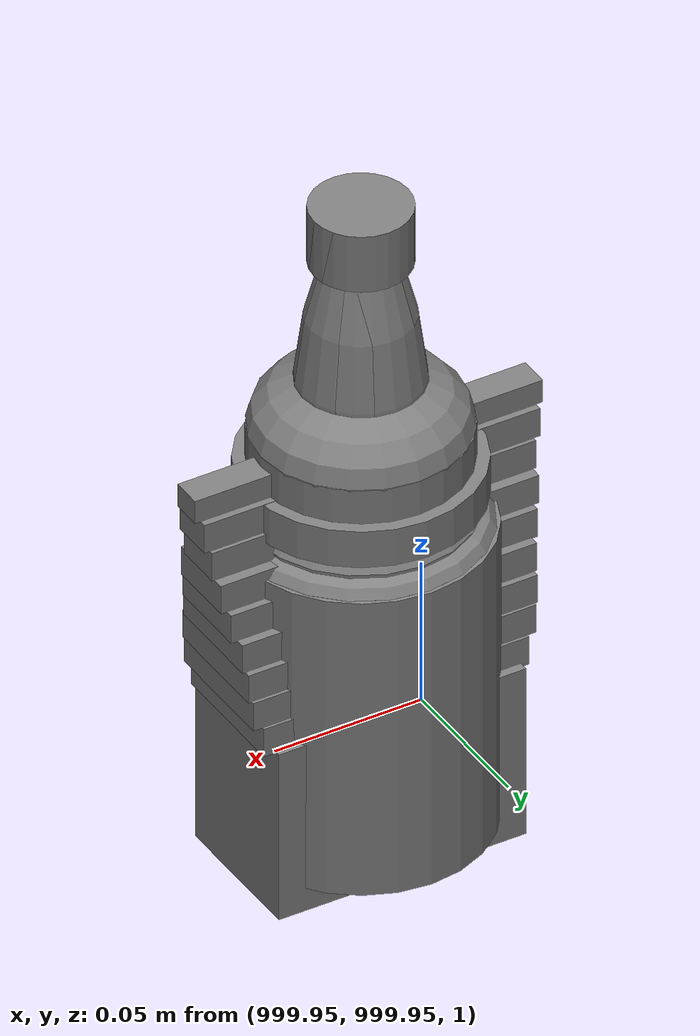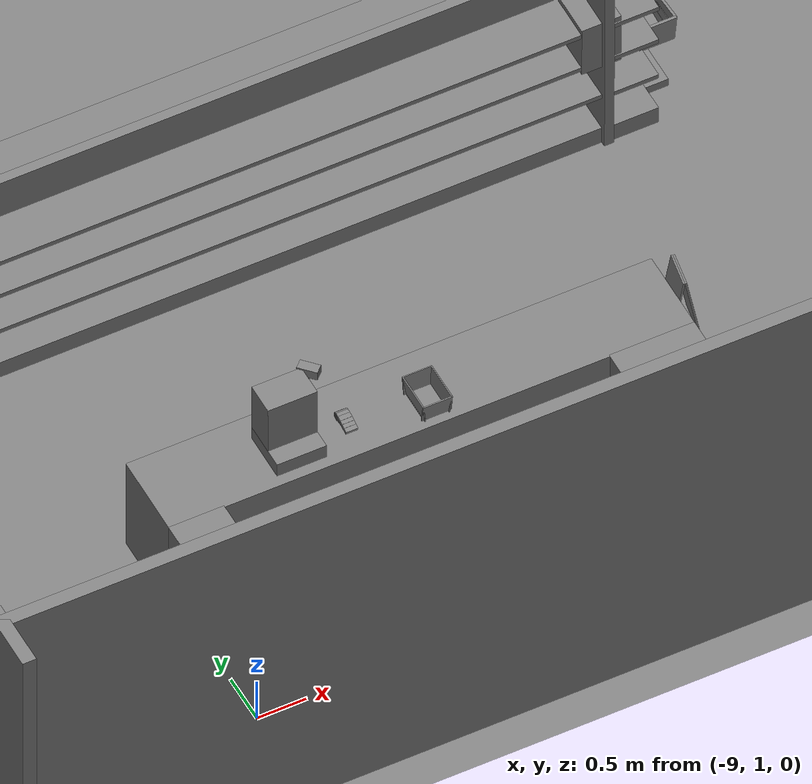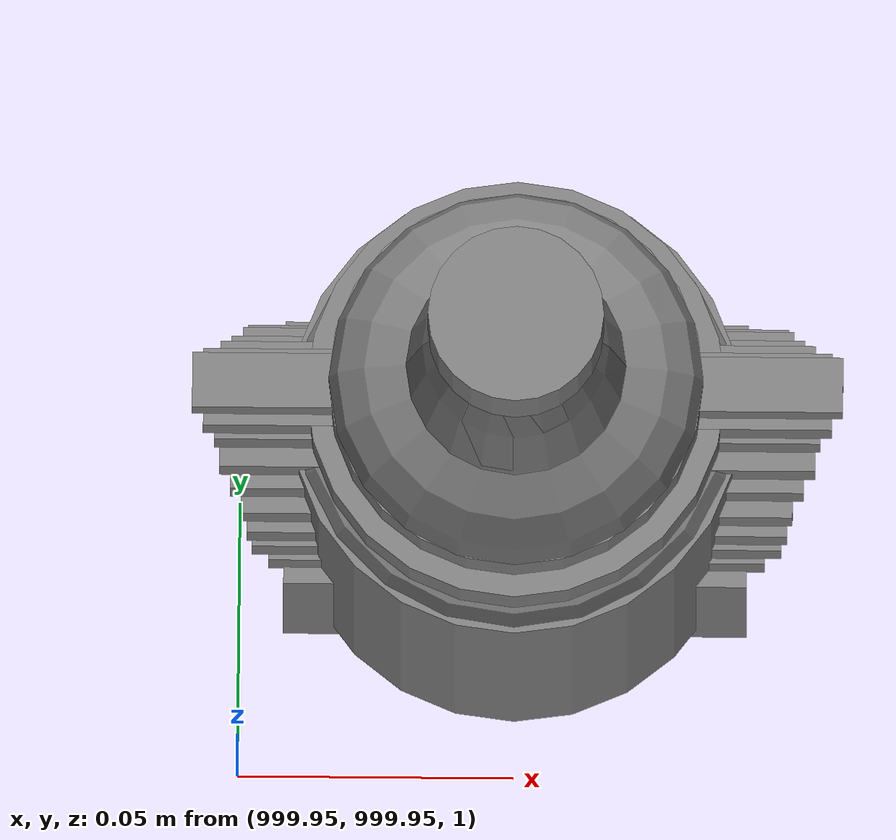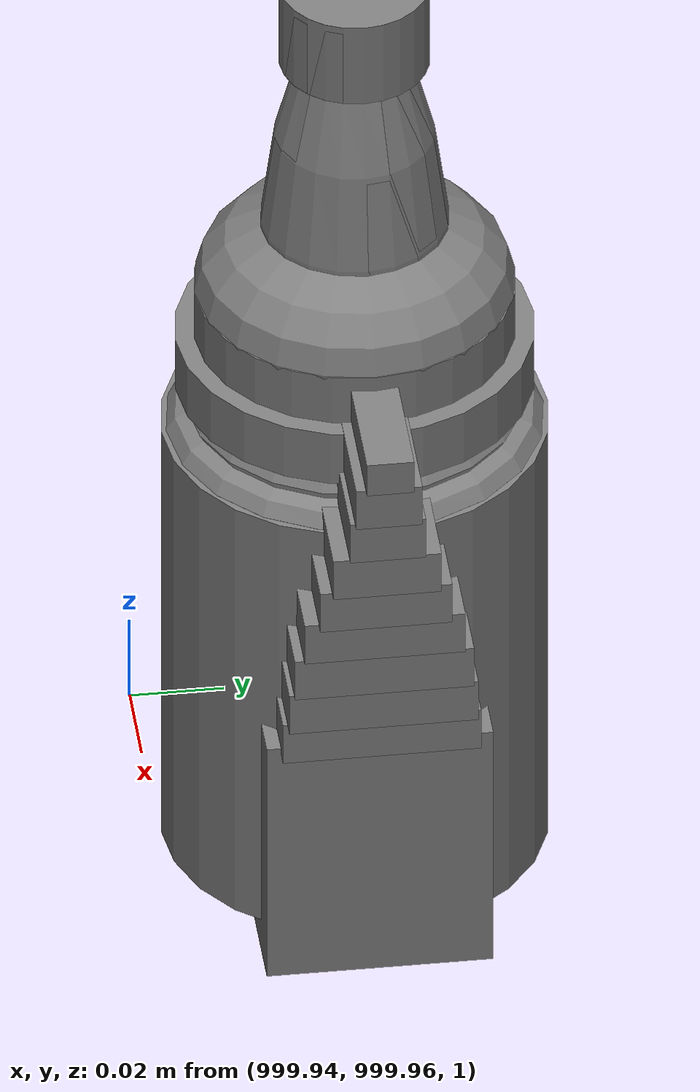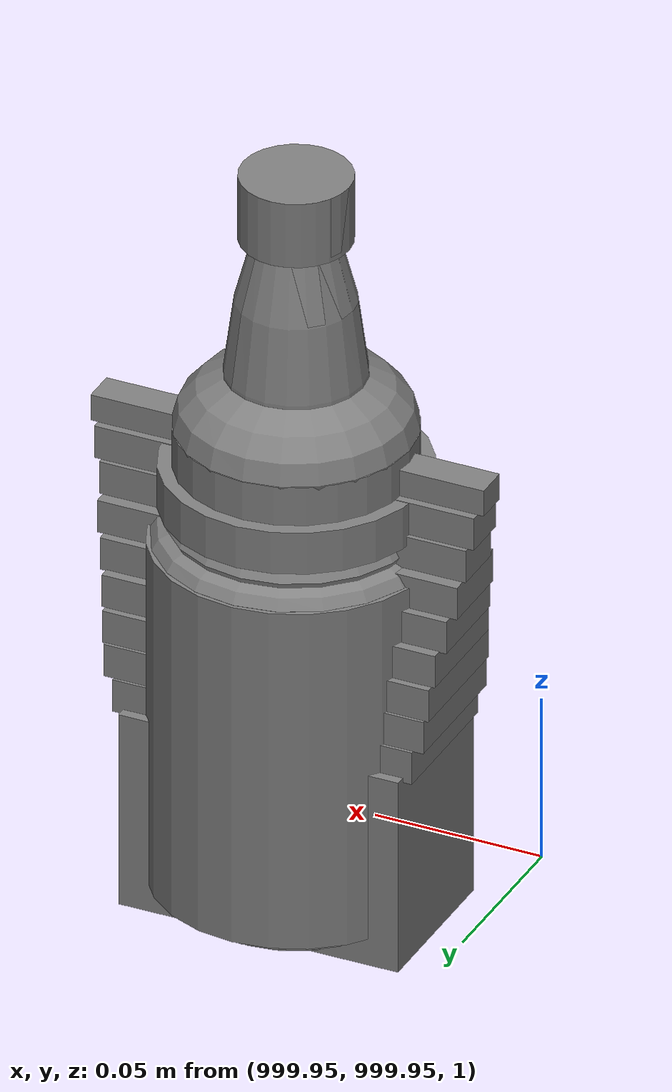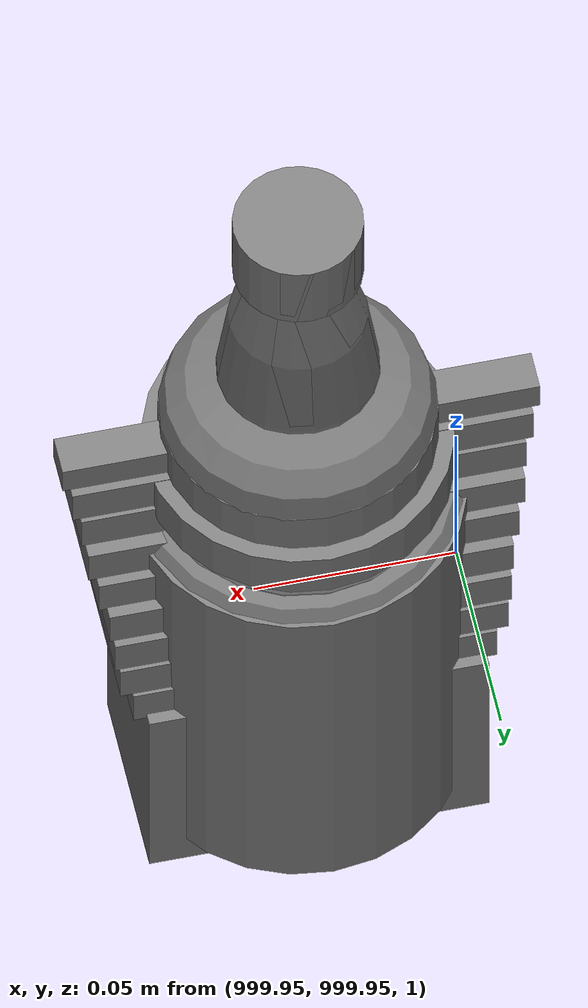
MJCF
<mujoco>
    <option gravity="0.000000000 0.000000000 -9.810000420" timestep="0.0166666" integrator="implicitfast" density="1.225" viscosity="1.8000001e-05" noslip_iterations="10" iterations="100" sdf_iterations="50">
        <flag multiccd="disable"/>
    </option>
    <size memory="1000M"/>
    <compiler coordinate="local"/>
    <worldbody>
        <light cutoff="30" pos="0 1 1" dir="0 -1 -2"/>
        <light cutoff="30" pos="0 -1 1" dir="0 1 -2"/>
        <body pos="0.000000000 0.000000000 0.000000000" euler="0.000000000 0.000000000 0.000000000" name="Interactive Objects_Interactive Objects"/>
        <body pos="1000.000000000 1000.000000000 1.000000000" euler="0.000000000 0.000000000 0.000000000" name="openloong_gripper_2f85_fix_base_usda_can">
            <geom contype="1" conaffinity="1" density="1000" type="cylinder" material="" rgba="0.500000000 0.500000000 0.500000000 1.000000000" solimp="0.899999976 0.949999988 0.001000000" friction="1.000000000 0.005000000 0.000100000" solref="0.020000000 1.000000000" margin="0" condim="3" group="0" pos="0.000000000 0.000000000 0.079676986" quat="1.000000000 0.000000000 0.000000000 0.000000000" size="0.034000002 0.071999997 1.000000000" name="openloong_gripper_2f85_fix_base_usda_geom_6033C467_C9C8_4116_B467_403C68ADF55D"/>
            <geom contype="1" conaffinity="1" density="1000" type="ellipsoid" material="" rgba="0.500000000 0.500000000 0.500000000 1.000000000" solimp="0.899999976 0.949999988 0.001000000" friction="1.000000000 0.005000000 0.000100000" solref="0.020000000 1.000000000" margin="0" condim="3" group="0" pos="0.000000000 0.000000000 0.151854277" quat="1.000000000 0.000000000 0.000000000 0.000000000" size="0.034000002 0.034000002 0.020000000" name="openloong_gripper_2f85_fix_base_usda_geom_5ED7661E_6064_45E8_8DFE_6A680F926730"/>
            <geom contype="1" conaffinity="1" density="1000" type="box" material="" rgba="0.500000000 0.500000000 0.500000000 1.000000000" solimp="0.899999976 0.949999988 0.001000000" friction="1.000000000 0.005000000 0.000100000" solref="0.020000000 1.000000000" margin="0" condim="3" group="0" pos="0.000000000 0.000000000 0.004777670" quat="1.000000000 0.000000000 0.000000000 0.000000000" size="0.020000000 0.020000000 0.005000000" name="openloong_gripper_2f85_fix_base_usda_geom_B903C2CA_49A1_4FCF_8E20_DA8160C8A3CF"/>
            <freejoint name="openloong_gripper_2f85_fix_base_usda_can_joint"/>
            <site size="0.005000000 0.005000000 0.005000000" rgba="0.500000000 0.500000000 0.500000000 1.000000000" pos="0.000000000 0.000000000 0.000000000" quat="1.000000000 0.000000000 0.000000000 0.000000000" group="0" type="sphere" name="openloong_gripper_2f85_fix_base_usda_cansite"/>
        </body>
        <body pos="1000.000000000 1000.000000000 1.000000000" euler="0.000000000 0.000000000 0.000000000" name="openloong_gripper_2f85_fix_base_usda_bottle_red">
            <geom contype="1" conaffinity="1" density="1000" type="ellipsoid" material="" rgba="0.500000000 0.500000000 0.500000000 1.000000000" solimp="0.899999976 0.949999988 0.001000000" friction="1.000000000 0.005000000 0.000100000" solref="0.020000000 1.000000000" margin="0" condim="3" group="0" pos="0.000000000 0.000000000 0.144284487" quat="1.000000000 0.000000000 0.000000000 0.000000000" size="0.021000000 0.021000000 0.079999998" name="openloong_gripper_2f85_fix_base_usda_geom_1EC75393_B6D2_41E3_BFB6_049817CFCEDB"/>
            <geom contype="1" conaffinity="1" density="1000" type="cylinder" material="" rgba="0.500000000 0.500000000 0.500000000 1.000000000" solimp="0.899999976 0.949999988 0.001000000" friction="1.000000000 0.005000000 0.000100000" solref="0.020000000 1.000000000" margin="0" condim="3" group="0" pos="0.000000000 0.000000000 0.220618963" quat="1.000000000 0.000000000 0.000000000 0.000000000" size="0.016000001 0.010000000 1.000000000" name="openloong_gripper_2f85_fix_base_usda_geom_A265B3E4_65D4_4099_9C90_28917D6BB512"/>
            <geom contype="1" conaffinity="1" density="1000" type="ellipsoid" material="" rgba="0.500000000 0.500000000 0.500000000 1.000000000" solimp="0.899999976 0.949999988 0.001000000" friction="1.000000000 0.005000000 0.000100000" solref="0.020000000 1.000000000" margin="0" condim="3" group="0" pos="0.000000000 0.000000000 0.118945479" quat="1.000000000 0.000000000 0.000000000 0.000000000" size="0.030999999 0.030999999 0.029999999" name="openloong_gripper_2f85_fix_base_usda_geom_37FCEA59_8ED9_4E5D_A8F0_C57538EC22B0"/>
            <geom contype="1" conaffinity="1" density="1000" type="box" material="" rgba="0.500000000 0.500000000 0.500000000 1.000000000" solimp="0.899999976 0.949999988 0.001000000" friction="1.000000000 0.005000000 0.000100000" solref="0.020000000 1.000000000" margin="0" condim="3" group="0" pos="0.000000000 0.000000000 0.002189159" quat="1.000000000 0.000000000 0.000000000 0.000000000" size="0.020000000 0.020000000 0.003000000" name="openloong_gripper_2f85_fix_base_usda_geom_C1C32A87_BDD1_4712_A374_3B9D07428CB5"/>
            <geom contype="1" conaffinity="1" density="1000" type="cylinder" material="" rgba="0.500000000 0.500000000 0.500000000 1.000000000" solimp="0.899999976 0.949999988 0.001000000" friction="1.000000000 0.005000000 0.000100000" solref="0.020000000 1.000000000" margin="0" condim="3" group="0" pos="0.000000000 -0.000366211 0.060884237" quat="1.000000000 0.000000000 0.000000000 0.000000000" size="0.030999999 0.057999998 1.000000000" name="openloong_gripper_2f85_fix_base_usda_geom_14F33C90_9431_4A0C_91C9_544D59D4FB47"/>
            <freejoint name="openloong_gripper_2f85_fix_base_usda_bottle_red_joint"/>
            <site size="0.005000000 0.005000000 0.005000000" rgba="0.500000000 0.500000000 0.500000000 1.000000000" pos="0.000000000 0.000000000 0.000000000" quat="0.999961913 0.008726535 0.000000000 0.000000000" group="0" type="sphere" name="openloong_gripper_2f85_fix_base_usda_bottle_redsite"/>
        </body>
        <body pos="1000.000000000 1000.000000000 1.000000000" euler="0.000000000 0.000000000 0.000000000" name="openloong_gripper_2f85_fix_base_usda_jar_01">
            <geom contype="1" conaffinity="1" density="1000" type="box" material="" rgba="0.500000000 0.500000000 0.500000000 1.000000000" solimp="0.899999976 0.949999988 0.001000000" friction="1.000000000 0.005000000 0.000100000" solref="0.020000000 1.000000000" margin="0" condim="3" group="0" pos="0.000000000 0.000000000 0.006158113" quat="1.000000000 0.000000000 0.000000000 0.000000000" size="0.020000000 0.020000000 0.005000000" name="openloong_gripper_2f85_fix_base_usda_geom_D448F17A_EF09_4E32_A010_A747AF2C1190"/>
            <geom contype="1" conaffinity="1" density="1000" type="cylinder" material="" rgba="0.500000000 0.500000000 0.500000000 1.000000000" solimp="0.899999976 0.949999988 0.001000000" friction="1.000000000 0.005000000 0.000100000" solref="0.020000000 1.000000000" margin="0" condim="3" group="0" pos="0.000000000 0.000000000 0.062744498" quat="1.000000000 0.000000000 0.000000000 0.000000000" size="0.041000001 0.052999999 1.000000000" name="openloong_gripper_2f85_fix_base_usda_geom_2025F172_E8F6_430A_9F2B_3D4520257B38"/>
            <geom contype="1" conaffinity="1" density="1000" type="ellipsoid" material="" rgba="0.500000000 0.500000000 0.500000000 1.000000000" solimp="0.899999976 0.949999988 0.001000000" friction="1.000000000 0.005000000 0.000100000" solref="0.020000000 1.000000000" margin="0" condim="3" group="0" pos="0.000000000 0.000000000 0.122252703" quat="1.000000000 0.000000000 0.000000000 0.000000000" size="0.035999998 0.035999998 0.010000000" name="openloong_gripper_2f85_fix_base_usda_geom_DE5B3BD9_86BB_48AB_BE17_378C9A54DE7C"/>
            <geom contype="1" conaffinity="1" density="1000" type="cylinder" material="" rgba="0.500000000 0.500000000 0.500000000 1.000000000" solimp="0.899999976 0.949999988 0.001000000" friction="1.000000000 0.005000000 0.000100000" solref="0.020000000 1.000000000" margin="0" condim="3" group="0" pos="0.000000000 0.000000000 0.015747190" quat="1.000000000 0.000000000 0.000000000 0.000000000" size="0.035000000 0.010000000 1.000000000" name="openloong_gripper_2f85_fix_base_usda_geom_7CCB5093_68A3_4235_854C_B7F8E4CDEF74"/>
            <geom contype="1" conaffinity="1" density="1000" type="ellipsoid" material="" rgba="0.500000000 0.500000000 0.500000000 1.000000000" solimp="0.899999976 0.949999988 0.001000000" friction="1.000000000 0.005000000 0.000100000" solref="0.020000000 1.000000000" margin="0" condim="3" group="0" pos="0.000000000 0.000000000 0.115815401" quat="1.000000000 0.000000000 0.000000000 0.000000000" size="0.039999999 0.039999999 0.010000000" name="openloong_gripper_2f85_fix_base_usda_geom_4A203FE6_DBA0_4CC7_B5BC_9B7CA11C4F99"/>
            <geom contype="1" conaffinity="1" density="1000" type="cylinder" material="" rgba="0.500000000 0.500000000 0.500000000 1.000000000" solimp="0.899999976 0.949999988 0.001000000" friction="1.000000000 0.005000000 0.000100000" solref="0.020000000 1.000000000" margin="0" condim="3" group="0" pos="0.000000000 0.000000000 0.133183479" quat="1.000000000 0.000000000 0.000000000 0.000000000" size="0.037999999 0.006500000 1.000000000" name="openloong_gripper_2f85_fix_base_usda_geom_5C805EE1_1566_4D85_80F9_F4347FFDC839"/>
            <freejoint name="openloong_gripper_2f85_fix_base_usda_jar_01_joint"/>
            <site size="0.005000000 0.005000000 0.005000000" rgba="0.500000000 0.500000000 0.500000000 1.000000000" pos="0.000000000 0.000000000 0.000000000" quat="1.000000000 0.000000000 0.000000000 0.000000000" group="0" type="sphere" name="openloong_gripper_2f85_fix_base_usda_jar_01site"/>
        </body>
        <body pos="1000.000000000 1000.000000000 1.000000000" euler="0.000000000 0.000000000 0.000000000" name="openloong_gripper_2f85_fix_base_usda_bottle_blue">
            <geom contype="1" conaffinity="1" density="1000" type="ellipsoid" material="" rgba="0.500000000 0.500000000 0.500000000 1.000000000" solimp="0.899999976 0.949999988 0.001000000" friction="1.000000000 0.005000000 0.000100000" solref="0.020000000 1.000000000" margin="0" condim="3" group="0" pos="0.000000000 0.000000000 0.118920922" quat="1.000000000 0.000000000 0.000000000 0.000000000" size="0.030999999 0.030999999 0.029999999" name="openloong_gripper_2f85_fix_base_usda_geom_F9E21ED3_F6BD_4181_AEB3_588889BBB72E"/>
            <geom contype="1" conaffinity="1" density="1000" type="box" material="" rgba="0.500000000 0.500000000 0.500000000 1.000000000" solimp="0.899999976 0.949999988 0.001000000" friction="1.000000000 0.005000000 0.000100000" solref="0.020000000 1.000000000" margin="0" condim="3" group="0" pos="0.000000000 0.000000000 0.002164602" quat="1.000000000 0.000000000 0.000000000 0.000000000" size="0.020000000 0.020000000 0.003000000" name="openloong_gripper_2f85_fix_base_usda_geom_F9B76280_C056_4A21_B5C3_13736FB46CB2"/>
            <geom contype="1" conaffinity="1" density="1000" type="cylinder" material="" rgba="0.500000000 0.500000000 0.500000000 1.000000000" solimp="0.899999976 0.949999988 0.001000000" friction="1.000000000 0.005000000 0.000100000" solref="0.020000000 1.000000000" margin="0" condim="3" group="0" pos="0.000000000 -0.000366211 0.060859680" quat="1.000000000 0.000000000 0.000000000 0.000000000" size="0.030999999 0.057999998 1.000000000" name="openloong_gripper_2f85_fix_base_usda_geom_E9A2B2EE_FB7E_45B1_AE72_8A279EDF14D1"/>
            <geom contype="1" conaffinity="1" density="1000" type="cylinder" material="" rgba="0.500000000 0.500000000 0.500000000 1.000000000" solimp="0.899999976 0.949999988 0.001000000" friction="1.000000000 0.005000000 0.000100000" solref="0.020000000 1.000000000" margin="0" condim="3" group="0" pos="0.000000000 0.000000000 0.220594406" quat="1.000000000 0.000000000 0.000000000 0.000000000" size="0.016000001 0.010000000 1.000000000" name="openloong_gripper_2f85_fix_base_usda_geom_7BC059F1_7285_4A0F_B6E7_FADE4A0C33AA"/>
            <geom contype="1" conaffinity="1" density="1000" type="ellipsoid" material="" rgba="0.500000000 0.500000000 0.500000000 1.000000000" solimp="0.899999976 0.949999988 0.001000000" friction="1.000000000 0.005000000 0.000100000" solref="0.020000000 1.000000000" margin="0" condim="3" group="0" pos="0.000000000 0.000000000 0.144259930" quat="1.000000000 0.000000000 0.000000000 0.000000000" size="0.021000000 0.021000000 0.079999998" name="openloong_gripper_2f85_fix_base_usda_geom_3D5515D4_D951_4312_A042_DD615AD6B940"/>
            <freejoint name="openloong_gripper_2f85_fix_base_usda_bottle_blue_joint"/>
            <site size="0.005000000 0.005000000 0.005000000" rgba="0.500000000 0.500000000 0.500000000 1.000000000" pos="0.000000000 0.000000000 0.000000000" quat="0.999961913 0.008726535 0.000000000 0.000000000" group="0" type="sphere" name="openloong_gripper_2f85_fix_base_usda_bottle_bluesite"/>
        </body>
        <body pos="-2.226759195 6.460038662 1.786314130" euler="-159.649780273 52.438137054 108.947738647" mocap="true" name="spotlight5_SpotLight"/>
        <body pos="-2.326236486 6.201567650 1.687896967" euler="5.328414917 41.537776947 -176.914382935" mocap="true" name="spotlight6_SpotLight"/>
        <body pos="1000.000000000 1000.000000000 1.000000000" euler="0.000000000 0.000000000 0.000000000" name="openloong_gripper_2f85_fix_base_usda_salt">
            <geom contype="1" conaffinity="1" density="1000" type="box" material="" rgba="0.500000000 0.500000000 0.500000000 1.000000000" solimp="0.899999976 0.949999988 0.001000000" friction="1.000000000 0.005000000 0.000100000" solref="0.020000000 1.000000000" margin="0" condim="3" group="0" pos="0.000305176 0.000000000 0.084862232" quat="1.000000000 0.000000000 0.000000000 0.000000000" size="0.048999999 0.018999999 0.005000000" name="openloong_gripper_2f85_fix_base_usda_geom_8E2FA526_9696_4524_BE74_E4CFE5CF0662"/>
            <geom contype="1" conaffinity="1" density="1000" type="box" material="" rgba="0.500000000 0.500000000 0.500000000 1.000000000" solimp="0.899999976 0.949999988 0.001000000" friction="1.000000000 0.005000000 0.000100000" solref="0.020000000 1.000000000" margin="0" condim="3" group="0" pos="0.000305176 0.000000000 0.104564309" quat="1.000000000 0.000000000 0.000000000 0.000000000" size="0.052000001 0.014000000 0.005000000" name="openloong_gripper_2f85_fix_base_usda_geom_2BF82FCA_3B21_4805_B44E_909B66B1E359"/>
            <geom contype="1" conaffinity="1" density="1000" type="box" material="" rgba="0.500000000 0.500000000 0.500000000 1.000000000" solimp="0.899999976 0.949999988 0.001000000" friction="1.000000000 0.005000000 0.000100000" solref="0.020000000 1.000000000" margin="0" condim="3" group="0" pos="0.000305176 0.000000000 0.114487171" quat="1.000000000 0.000000000 0.000000000 0.000000000" size="0.054000001 0.011500000 0.005000000" name="openloong_gripper_2f85_fix_base_usda_geom_8469B031_B6A8_4FBA_AEE0_0AE4595FC01C"/>
            <geom contype="1" conaffinity="1" density="1000" type="box" material="" rgba="0.500000000 0.500000000 0.500000000 1.000000000" solimp="0.899999976 0.949999988 0.001000000" friction="1.000000000 0.005000000 0.000100000" solref="0.020000000 1.000000000" margin="0" condim="3" group="0" pos="0.000305176 0.000000000 0.075103164" quat="1.000000000 0.000000000 0.000000000 0.000000000" size="0.048000000 0.020000000 0.005000000" name="openloong_gripper_2f85_fix_base_usda_geom_31756A70_8B14_4408_BF78_66FCDD1DB7AE"/>
            <geom contype="1" conaffinity="1" density="1000" type="box" material="" rgba="0.500000000 0.500000000 0.500000000 1.000000000" solimp="0.899999976 0.949999988 0.001000000" friction="1.000000000 0.005000000 0.000100000" solref="0.020000000 1.000000000" margin="0" condim="3" group="0" pos="0.000305176 0.000000000 0.134892464" quat="1.000000000 0.000000000 0.000000000 0.000000000" size="0.057000000 0.007000000 0.005000000" name="openloong_gripper_2f85_fix_base_usda_geom_006E92C5_8E97_401A_AEFE_71799A3475D4"/>
            <geom contype="1" conaffinity="1" density="1000" type="box" material="" rgba="0.500000000 0.500000000 0.500000000 1.000000000" solimp="0.899999976 0.949999988 0.001000000" friction="1.000000000 0.005000000 0.000100000" solref="0.020000000 1.000000000" margin="0" condim="3" group="0" pos="0.000305176 0.000000000 0.094920278" quat="1.000000000 0.000000000 0.000000000 0.000000000" size="0.050000001 0.017000001 0.005000000" name="openloong_gripper_2f85_fix_base_usda_geom_62E7692C_6D99_4B24_80FC_7245D6CCA1A1"/>
            <geom contype="1" conaffinity="1" density="1000" type="box" material="" rgba="0.500000000 0.500000000 0.500000000 1.000000000" solimp="0.899999976 0.949999988 0.001000000" friction="1.000000000 0.005000000 0.000100000" solref="0.020000000 1.000000000" margin="0" condim="3" group="0" pos="0.000305176 0.000000000 0.065204859" quat="1.000000000 0.000000000 0.000000000 0.000000000" size="0.045000002 0.021000000 0.005000000" name="openloong_gripper_2f85_fix_base_usda_geom_50AFF5AA_AE1D_4C72_99EE_BF54047424D0"/>
            <geom contype="1" conaffinity="1" density="1000" type="box" material="" rgba="0.500000000 0.500000000 0.500000000 1.000000000" solimp="0.899999976 0.949999988 0.001000000" friction="1.000000000 0.005000000 0.000100000" solref="0.020000000 1.000000000" margin="0" condim="3" group="0" pos="0.000305176 0.000000000 0.144135714" quat="1.000000000 0.000000000 0.000000000 0.000000000" size="0.059000000 0.005000000 0.004000000" name="openloong_gripper_2f85_fix_base_usda_geom_F5396538_EED7_454B_936E_F956D1EEEF3A"/>
            <geom contype="1" conaffinity="1" density="1000" type="box" material="" rgba="0.500000000 0.500000000 0.500000000 1.000000000" solimp="0.899999976 0.949999988 0.001000000" friction="1.000000000 0.005000000 0.000100000" solref="0.020000000 1.000000000" margin="0" condim="3" group="0" pos="0.000000000 0.000000000 0.031593561" quat="1.000000000 0.000000000 0.000000000 0.000000000" size="0.041999999 0.024000000 0.029999999" name="openloong_gripper_2f85_fix_base_usda_geom_F5B20687_DB66_49EE_8800_0A97126EAC57"/>
            <geom contype="1" conaffinity="1" density="1000" type="box" material="" rgba="0.500000000 0.500000000 0.500000000 1.000000000" solimp="0.899999976 0.949999988 0.001000000" friction="1.000000000 0.005000000 0.000100000" solref="0.020000000 1.000000000" margin="0" condim="3" group="0" pos="0.000305176 0.000000000 0.124608755" quat="1.000000000 0.000000000 0.000000000 0.000000000" size="0.055000000 0.008000000 0.005000000" name="openloong_gripper_2f85_fix_base_usda_geom_FA026A27_379C_4D7A_8D13_F08768EA73EF"/>
            <freejoint name="openloong_gripper_2f85_fix_base_usda_salt_joint"/>
            <site size="0.005000000 0.005000000 0.005000000" rgba="0.500000000 0.500000000 0.500000000 1.000000000" pos="0.000000000 0.000000000 0.000000000" quat="1.000000000 0.000000000 0.000000000 0.000000000" group="0" type="sphere" name="openloong_gripper_2f85_fix_base_usda_saltsite"/>
        </body>
        <body pos="-1.888133168 6.351180553 1.751451612" euler="-144.728912354 32.786026001 45.893146515" mocap="true" name="spotlight4_SpotLight"/>
        <body pos="0.000000000 0.000000000 0.000000000" euler="0.000000000 0.000000000 0.000000000" name=" Static Objects_ Static Objects">
            <geom contype="1" conaffinity="1" density="1000" type="box" material="" rgba="0.500000000 0.500000000 0.500000000 1.000000000" solimp="0.899999976 0.949999988 0.001000000" friction="1.000000000 0.005000000 0.000100000" solref="0.020000000 1.000000000" margin="0" condim="3" group="0" pos="-6.286010742 6.153595448 1.563861728" quat="0.707107067 0.000000000 0.000000000 0.707106471" size="0.529999971 3.134999990 0.025000000" name=" Static Objects_geom_3270974F_966C_4EEE_AD4E_1A647021B7FF"/>
            <geom contype="1" conaffinity="1" density="1000" type="box" material="" rgba="0.500000000 0.500000000 0.500000000 1.000000000" solimp="0.899999976 0.949999988 0.001000000" friction="1.000000000 0.005000000 0.000100000" solref="0.020000000 1.000000000" margin="0" condim="3" group="0" pos="-3.101639986 6.150595188 1.018643856" quat="1.000000000 0.000000000 0.000000000 0.000000000" size="0.050000001 0.579999983 1.019999981" name=" Static Objects_geom_D99D9CB0_A97B_4AD9_ACC9_5F8598726C93"/>
            <geom contype="1" conaffinity="1" density="1000" type="box" material="" rgba="0.500000000 0.500000000 0.500000000 1.000000000" solimp="0.899999976 0.949999988 0.001000000" friction="1.000000000 0.005000000 0.000100000" solref="0.020000000 1.000000000" margin="0" condim="3" group="0" pos="-2.825197220 6.153595448 1.563861728" quat="0.707107067 0.000000000 0.000000000 0.707106471" size="0.550000012 0.239999995 0.025000000" name=" Static Objects_geom_E153678E_C54D_4536_8005_4B798635750C"/>
            <geom contype="1" conaffinity="1" density="1000" type="box" material="" rgba="0.500000000 0.500000000 0.500000000 1.000000000" solimp="0.899999976 0.949999988 0.001000000" friction="1.000000000 0.005000000 0.000100000" solref="0.020000000 1.000000000" margin="0" condim="3" group="0" pos="-6.311686516 6.153595448 1.018643856" quat="0.707107067 0.000000000 0.000000000 0.707106471" size="0.050000001 3.150000095 1.019999981" name=" Static Objects_geom_05C85C15_D3B1_4012_B199_CDDE2BA310A9"/>
            <geom contype="1" conaffinity="1" density="1000" type="box" material="" rgba="0.500000000 0.500000000 0.500000000 1.000000000" solimp="0.899999976 0.949999988 0.001000000" friction="1.000000000 0.005000000 0.000100000" solref="0.020000000 1.000000000" margin="0" condim="3" group="0" pos="-2.825197220 6.153595448 1.115278244" quat="0.707107067 0.000000000 0.000000000 0.707106471" size="0.550000012 0.239999995 0.025000000" name=" Static Objects_geom_D52E16F6_18CB_4399_A6C7_DF899B5885C3"/>
            <geom contype="1" conaffinity="1" density="1000" type="box" material="" rgba="0.500000000 0.500000000 0.500000000 1.000000000" solimp="0.899999976 0.949999988 0.001000000" friction="1.000000000 0.005000000 0.000100000" solref="0.020000000 1.000000000" margin="0" condim="3" group="0" pos="-6.293097973 6.153595448 1.114443064" quat="0.707107067 0.000000000 0.000000000 0.707106471" size="0.529999971 3.134999990 0.025000000" name=" Static Objects_geom_65481054_57B0_4D26_A634_9CFBEE651E52"/>
            <geom contype="1" conaffinity="1" density="1000" type="box" material="" rgba="0.500000000 0.500000000 0.500000000 1.000000000" solimp="0.899999976 0.949999988 0.001000000" friction="1.000000000 0.005000000 0.000100000" solref="0.020000000 1.000000000" margin="0" condim="3" group="0" pos="-2.825197220 6.153595448 0.629031777" quat="0.707107067 0.000000000 0.000000000 0.707106471" size="0.550000012 0.239999995 0.025000000" name=" Static Objects_geom_B530D45D_7B66_4628_8914_B0EED498F464"/>
            <geom contype="1" conaffinity="1" density="1000" type="box" material="" rgba="0.500000000 0.500000000 0.500000000 1.000000000" solimp="0.899999976 0.949999988 0.001000000" friction="1.000000000 0.005000000 0.000100000" solref="0.020000000 1.000000000" margin="0" condim="3" group="0" pos="-6.286010742 6.153595448 0.096129179" quat="0.707107067 0.000000000 0.000000000 0.707106471" size="0.529999971 3.134999990 0.098999999" name=" Static Objects_geom_1BC49E86_0990_47D3_AE7A_DD2169A28982"/>
            <geom contype="1" conaffinity="1" density="1000" type="box" material="" rgba="0.500000000 0.500000000 0.500000000 1.000000000" solimp="0.899999976 0.949999988 0.001000000" friction="1.000000000 0.005000000 0.000100000" solref="0.020000000 1.000000000" margin="0" condim="3" group="0" pos="-2.825197220 6.153595448 0.097434282" quat="0.707107067 0.000000000 0.000000000 0.707106471" size="0.550000012 0.239999995 0.098999999" name=" Static Objects_geom_D59B00E6_C490_46A0_ABA7_FC42A01810A0"/>
            <geom contype="1" conaffinity="1" density="1000" type="box" material="" rgba="0.500000000 0.500000000 0.500000000 1.000000000" solimp="0.899999976 0.949999988 0.001000000" friction="1.000000000 0.005000000 0.000100000" solref="0.020000000 1.000000000" margin="0" condim="3" group="0" pos="-6.286010742 6.153595448 0.629031777" quat="0.707107067 0.000000000 0.000000000 0.707106471" size="0.529999971 3.134999990 0.025000000" name=" Static Objects_geom_CA2DE2A4_556E_42FF_BAFF_51217977F789"/>
            <geom contype="1" conaffinity="1" density="1000" type="box" material="" rgba="0.500000000 0.500000000 0.500000000 1.000000000" solimp="0.899999976 0.949999988 0.001000000" friction="1.000000000 0.005000000 0.000100000" solref="0.020000000 1.000000000" margin="0" condim="3" group="0" pos="-6.000000000 20.159999847 2.000000000" quat="1.000000000 0.000000000 0.000000000 0.000000000" size="6.079999924 0.070000000 2.000000000" name=" Static Objects_geom_64539034_ABEF_4470_B2C1_7B6BCC31A9CC"/>
            <geom contype="1" conaffinity="1" density="1000" type="box" material="" rgba="0.500000000 0.500000000 0.500000000 1.000000000" solimp="0.899999976 0.949999988 0.001000000" friction="1.000000000 0.005000000 0.000100000" solref="0.020000000 1.000000000" margin="0" condim="3" group="0" pos="-6.000000000 0.035000000 2.000000000" quat="1.000000000 0.000000000 0.000000000 0.000000000" size="6.079999924 0.070000000 2.000000000" name=" Static Objects_geom_DB732F9A_D2C3_434A_B95E_C37B50E95181"/>
            <geom contype="1" conaffinity="1" density="1000" type="box" material="" rgba="0.500000000 0.500000000 0.500000000 1.000000000" solimp="0.899999976 0.949999988 0.001000000" friction="1.000000000 0.005000000 0.000100000" solref="0.020000000 1.000000000" margin="0" condim="3" group="0" pos="0.000000000 10.000000000 2.000000000" quat="1.000000000 0.000000000 0.000000000 0.000000000" size="0.070000000 10.500000000 2.000000000" name=" Static Objects_geom_5B0688BC_66A5_4DEF_A05C_F0CDC15B9B44"/>
            <geom contype="1" conaffinity="1" density="1000" type="box" material="" rgba="0.500000000 0.500000000 0.500000000 1.000000000" solimp="0.899999976 0.949999988 0.001000000" friction="1.000000000 0.005000000 0.000100000" solref="0.020000000 1.000000000" margin="0" condim="3" group="0" pos="-12.050000191 10.000000000 2.000000000" quat="1.000000000 0.000000000 0.000000000 0.000000000" size="0.070000000 10.500000000 2.000000000" name=" Static Objects_geom_058C2FFB_1F90_4F37_B450_D787D73EFED8"/>
            <geom contype="1" conaffinity="1" density="1000" type="plane" material="" rgba="0.500000000 0.500000000 0.500000000 1.000000000" solimp="0.899999976 0.949999988 0.001000000" friction="1.000000000 0.005000000 0.000100000" solref="0.020000000 1.000000000" margin="0" condim="3" group="0" pos="-6.000000000 10.399999619 0.000000000" quat="1.000000000 0.000000000 0.000000000 0.000000000" size="6.050000191 10.800000191 0.010000000" name=" Static Objects_geom_09C0FD7D_E9AE_41DC_87BF_DC07D772F288"/>
            <geom contype="1" conaffinity="1" density="1000" type="box" material="" rgba="0.500000000 0.500000000 0.500000000 1.000000000" solimp="0.899999976 0.949999988 0.001000000" friction="1.000000000 0.005000000 0.000100000" solref="0.020000000 1.000000000" margin="0" condim="3" group="0" pos="-8.830721855 2.096410990 0.549305558" quat="1.000000000 0.000000000 0.000000000 0.000000000" size="0.280000001 0.430000007 0.550000012" name=" Static Objects_geom_D8B5C522_C47E_4403_AC50_6C553506BBF1"/>
            <geom contype="1" conaffinity="1" density="1000" type="box" material="" rgba="0.500000000 0.500000000 0.500000000 1.000000000" solimp="0.899999976 0.949999988 0.001000000" friction="1.000000000 0.005000000 0.000100000" solref="0.020000000 1.000000000" margin="0" condim="3" group="0" pos="-6.460197449 2.937205315 0.548931718" quat="1.000000000 0.000000000 0.000000000 0.000000000" size="2.650000095 0.430000007 0.550000012" name=" Static Objects_geom_1AD0DD71_FEC1_4A8D_B846_CB4F5C247516"/>
            <geom contype="1" conaffinity="1" density="1000" type="box" material="" rgba="0.500000000 0.500000000 0.500000000 1.000000000" solimp="0.899999976 0.949999988 0.001000000" friction="1.000000000 0.005000000 0.000100000" solref="0.020000000 1.000000000" margin="0" condim="3" group="0" pos="-4.240264893 1.327049494 0.549888909" quat="1.000000000 0.000000000 0.000000000 0.000000000" size="0.430000007 1.200000048 0.550000012" name=" Static Objects_geom_0E623025_3F31_4F89_991F_761CAA15B0E8"/>
            <geom contype="1" conaffinity="1" density="1000" type="box" material="" rgba="0.500000000 0.500000000 0.500000000 1.000000000" solimp="0.899999976 0.949999988 0.001000000" friction="1.000000000 0.005000000 0.000100000" solref="0.020000000 1.000000000" margin="0" condim="3" group="0" pos="-7.408766270 3.088089943 1.776644945" quat="0.928051054 0.000000000 0.000000000 0.372453064" size="0.050000001 0.100000001 0.050000001" name=" Static Objects_geom_2D2A7A9A_E6BD_4329_868F_968BB675C7AC"/>
            <geom contype="1" conaffinity="1" density="1000" type="box" material="" rgba="0.500000000 0.500000000 0.500000000 1.000000000" solimp="0.899999976 0.949999988 0.001000000" friction="1.000000000 0.005000000 0.000100000" solref="0.020000000 1.000000000" margin="0" condim="3" group="0" pos="-7.437745571 3.067511320 1.289965630" quat="1.000000000 0.000000000 0.000000000 0.000000000" size="0.029999999 0.020000000 0.020000000" name=" Static Objects_geom_CB45E5AC_3503_45A3_BDAE_3EA6583B723E"/>
            <geom contype="1" conaffinity="1" density="1000" type="box" material="" rgba="0.500000000 0.500000000 0.500000000 1.000000000" solimp="0.899999976 0.949999988 0.001000000" friction="1.000000000 0.005000000 0.000100000" solref="0.020000000 1.000000000" margin="0" condim="3" group="0" pos="-7.719123363 2.867671013 1.173410416" quat="1.000000000 0.000000000 0.000000000 0.000000000" size="0.250000000 0.250000000 0.079999998" name=" Static Objects_geom_F426F0EE_8A77_4C3A_88B6_C10A2F3004FA"/>
            <geom contype="1" conaffinity="1" density="1000" type="box" material="" rgba="0.500000000 0.500000000 0.500000000 1.000000000" solimp="0.899999976 0.949999988 0.001000000" friction="1.000000000 0.005000000 0.000100000" solref="0.020000000 1.000000000" margin="0" condim="3" group="0" pos="-7.719123363 2.958004713 1.530241251" quat="1.000000000 0.000000000 0.000000000 0.000000000" size="0.250000000 0.159999996 0.280000001" name=" Static Objects_geom_DCBD3E19_6970_4CBF_BE0F_EC84A3AE0F08"/>
            <geom contype="1" conaffinity="1" density="1000" type="cylinder" material="" rgba="0.500000000 0.500000000 0.500000000 1.000000000" solimp="0.899999976 0.949999988 0.001000000" friction="1.000000000 0.005000000 0.000100000" solref="0.020000000 1.000000000" margin="0" condim="3" group="0" pos="-7.427312374 3.069516420 1.502544641" quat="0.928051054 0.000000000 0.000000000 0.372453064" size="0.015000000 0.230000004 0.100000001" name=" Static Objects_geom_83555414_A8D1_472B_BAB9_22877F3ACB31"/>
            <geom contype="1" conaffinity="1" density="1000" type="box" material="" rgba="0.500000000 0.500000000 0.500000000 1.000000000" solimp="0.899999976 0.949999988 0.001000000" friction="1.000000000 0.005000000 0.000100000" solref="0.020000000 1.000000000" margin="0" condim="3" group="0" pos="-9.058088303 6.434794426 1.209077358" quat="1.000000000 0.000000000 0.000000000 0.000000000" size="0.250000000 0.100000001 0.070000000" name=" Static Objects_geom_8D01A5D1_62F0_4DD1_A50C_7D922EC063EB"/>
            <geom contype="1" conaffinity="1" density="1000" type="box" material="" rgba="0.500000000 0.500000000 0.500000000 1.000000000" solimp="0.899999976 0.949999988 0.001000000" friction="1.000000000 0.005000000 0.000100000" solref="0.020000000 1.000000000" margin="0" condim="3" group="0" pos="-5.611940861 6.318420410 0.350975692" quat="1.000000000 0.000000000 0.000000000 0.000000000" size="0.699999988 0.100000001 0.150000006" name=" Static Objects_geom_248316D4_FA4C_412A_BC9C_048A630D13B0"/>
            <geom contype="1" conaffinity="1" density="1000" type="box" material="" rgba="0.500000000 0.500000000 0.500000000 1.000000000" solimp="0.899999976 0.949999988 0.001000000" friction="1.000000000 0.005000000 0.000100000" solref="0.020000000 1.000000000" margin="0" condim="3" group="0" pos="-9.237723351 6.464855671 1.209077358" quat="1.000000000 0.000000000 0.000000000 0.000000000" size="0.100000001 0.100000001 0.070000000" name=" Static Objects_geom_93C54BB1_B050_4CB6_8589_6E06D6EC4180"/>
            <geom contype="1" conaffinity="1" density="1000" type="box" material="" rgba="0.500000000 0.500000000 0.500000000 1.000000000" solimp="0.899999976 0.949999988 0.001000000" friction="1.000000000 0.005000000 0.000100000" solref="0.020000000 1.000000000" margin="0" condim="3" group="0" pos="-6.300771236 6.459744930 1.744376063" quat="1.000000000 0.000000000 0.000000000 0.000000000" size="3.000000000 0.200000003 0.150000006" name=" Static Objects_geom_AE541FB7_5BEA_48A7_B0D1_AA6BAFD26E76"/>
            <geom contype="1" conaffinity="1" density="1000" type="box" material="" rgba="0.500000000 0.500000000 0.500000000 1.000000000" solimp="0.899999976 0.949999988 0.001000000" friction="1.000000000 0.005000000 0.000100000" solref="0.020000000 1.000000000" margin="0" condim="3" group="0" pos="-7.373087406 6.458900928 1.214329123" quat="1.000000000 0.000000000 0.000000000 0.000000000" size="0.250000000 0.200000003 0.075000003" name=" Static Objects_geom_42AD9E8F_E7A8_4D22_9A3C_C5C6EE7BBFA2"/>
            <geom contype="1" conaffinity="1" density="1000" type="box" material="" rgba="0.500000000 0.500000000 0.500000000 1.000000000" solimp="0.899999976 0.949999988 0.001000000" friction="1.000000000 0.005000000 0.000100000" solref="0.020000000 1.000000000" margin="0" condim="3" group="0" pos="-4.035642624 6.459744930 0.352518857" quat="1.000000000 0.000000000 0.000000000 0.000000000" size="0.800000012 0.200000003 0.150000006" name=" Static Objects_geom_F83A6CCE_AEE7_49C4_96C4_79B389625F8F"/>
            <geom contype="1" conaffinity="1" density="1000" type="box" material="" rgba="0.500000000 0.500000000 0.500000000 1.000000000" solimp="0.899999976 0.949999988 0.001000000" friction="1.000000000 0.005000000 0.000100000" solref="0.020000000 1.000000000" margin="0" condim="3" group="0" pos="-3.907610416 6.318625927 0.800981164" quat="1.000000000 0.000000000 0.000000000 0.000000000" size="0.500000000 0.100000001 0.150000006" name=" Static Objects_geom_5527FEE7_805A_4497_A1DE_FF5D505285D0"/>
            <geom contype="1" conaffinity="1" density="1000" type="box" material="" rgba="0.500000000 0.500000000 0.500000000 1.000000000" solimp="0.899999976 0.949999988 0.001000000" friction="1.000000000 0.005000000 0.000100000" solref="0.020000000 1.000000000" margin="0" condim="3" group="0" pos="-6.098561764 6.327973843 1.292199373" quat="1.000000000 0.000000000 0.000000000 0.000000000" size="0.500000000 0.100000001 0.150000006" name=" Static Objects_geom_59AECE79_D41D_4EF1_9E9C_6C4C98E35B05"/>
            <geom contype="1" conaffinity="1" density="1000" type="box" material="" rgba="0.500000000 0.500000000 0.500000000 1.000000000" solimp="0.899999976 0.949999988 0.001000000" friction="1.000000000 0.005000000 0.000100000" solref="0.020000000 1.000000000" margin="0" condim="3" group="0" pos="-7.886891365 6.459744930 0.352518857" quat="1.000000000 0.000000000 0.000000000 0.000000000" size="1.500000000 0.200000003 0.150000006" name=" Static Objects_geom_F6B96839_4EE2_4AAC_A28A_AD31721577D6"/>
            <geom contype="1" conaffinity="1" density="1000" type="box" material="" rgba="0.500000000 0.500000000 0.500000000 1.000000000" solimp="0.899999976 0.949999988 0.001000000" friction="1.000000000 0.005000000 0.000100000" solref="0.020000000 1.000000000" margin="0" condim="3" group="0" pos="-6.824534416 6.447464466 1.212718010" quat="1.000000000 0.000000000 0.000000000 0.000000000" size="0.100000001 0.100000001 0.075000003" name=" Static Objects_geom_0EE31E84_2E50_41D7_A0AF_3FA4D5256D1B"/>
            <geom contype="1" conaffinity="1" density="1000" type="box" material="" rgba="0.500000000 0.500000000 0.500000000 1.000000000" solimp="0.899999976 0.949999988 0.001000000" friction="1.000000000 0.005000000 0.000100000" solref="0.020000000 1.000000000" margin="0" condim="3" group="0" pos="-4.407354832 6.459744930 1.292199373" quat="1.000000000 0.000000000 0.000000000 0.000000000" size="1.240000010 0.200000003 0.150000006" name=" Static Objects_geom_1C14DA8B_D714_4A4F_ADB9_9FC3014CD09A"/>
            <geom contype="1" conaffinity="1" density="1000" type="box" material="" rgba="0.500000000 0.500000000 0.500000000 1.000000000" solimp="0.899999976 0.949999988 0.001000000" friction="1.000000000 0.005000000 0.000100000" solref="0.020000000 1.000000000" margin="0" condim="3" group="0" pos="-6.751636982 6.459744930 0.800981164" quat="1.000000000 0.000000000 0.000000000 0.000000000" size="2.200000048 0.200000003 0.150000006" name=" Static Objects_geom_16131F26_BA8A_403C_A03F_54101BA48BB5"/>
            <geom contype="1" conaffinity="1" density="1000" type="box" material="" rgba="0.500000000 0.500000000 0.500000000 1.000000000" solimp="0.899999976 0.949999988 0.001000000" friction="1.000000000 0.005000000 0.000100000" solref="0.020000000 1.000000000" margin="0" condim="3" group="0" pos="-6.924745083 6.362090111 1.214329123" quat="1.000000000 0.000000000 0.000000000 0.000000000" size="0.200000003 0.100000001 0.075000003" name=" Static Objects_geom_0157660C_E113_409E_A884_08FC9428E7A3"/>
            <geom contype="1" conaffinity="1" density="1000" type="box" material="" rgba="0.500000000 0.500000000 0.500000000 1.000000000" solimp="0.899999976 0.949999988 0.001000000" friction="1.000000000 0.005000000 0.000100000" solref="0.020000000 1.000000000" margin="0" condim="3" group="0" pos="-8.844120979 6.464855671 1.209077358" quat="1.000000000 0.000000000 0.000000000 0.000000000" size="0.100000001 0.100000001 0.070000000" name=" Static Objects_geom_E38A473A_3E21_425C_BD93_05C1CF27B791"/>
            <geom contype="1" conaffinity="1" density="1000" type="box" material="" rgba="0.500000000 0.500000000 0.500000000 1.000000000" solimp="0.899999976 0.949999988 0.001000000" friction="1.000000000 0.005000000 0.000100000" solref="0.020000000 1.000000000" margin="0" condim="3" group="0" pos="-3.157672644 6.136868477 1.348373055" quat="1.000000000 0.000000000 0.000000000 0.000000000" size="0.200000003 0.519999981 0.300000012" name=" Static Objects_geom_AB8B6132_D9FA_4C4B_A3EB_57AF228CA99A"/>
        </body>
        <body pos="-6.332345009 2.779978037 1.034067392" euler="0.000000000 0.000000000 0.000000000" name="openloong_gripper_2f85_fix_base_usda_basket">
            <geom contype="1" conaffinity="1" density="100000" type="box" material="" rgba="0.500000000 0.500000000 0.500000000 1.000000000" solimp="0.899999976 0.949999988 0.001000000" friction="1.000000000 0.899999976 0.000100000" solref="0.020000000 1.000000000" margin="0" condim="3" group="0" pos="-0.039724827 -0.188568115 0.167089701" quat="0.997537494 0.070135131 0.000000000 0.000000000" size="0.150000006 0.006000000 0.108000003" name="openloong_gripper_2f85_fix_base_usda_geom_A87FFE99_3D25_41F1_A0E0_FD74E5DA5032"/>
            <geom contype="1" conaffinity="1" density="100000" type="box" material="" rgba="0.500000000 0.500000000 0.500000000 1.000000000" solimp="0.899999976 0.949999988 0.001000000" friction="1.000000000 0.899999976 0.000100000" solref="0.020000000 1.000000000" margin="0" condim="3" group="0" pos="0.094372749 0.000000000 0.168361664" quat="0.706172049 0.036353335 0.036353379 0.706171215" size="0.200000003 0.006000000 0.108000003" name="openloong_gripper_2f85_fix_base_usda_geom_98B8B750_BE4B_4140_AE8B_0423D862002E"/>
            <geom contype="1" conaffinity="1" density="100000" type="box" material="" rgba="0.500000000 0.500000000 0.500000000 1.000000000" solimp="0.899999976 0.949999988 0.001000000" friction="1.000000000 0.899999976 0.000100000" solref="0.020000000 1.000000000" margin="0" condim="3" group="0" pos="-0.039724827 0.000000000 0.068126202" quat="1.000000000 0.000000000 0.000000000 0.000000000" size="0.129999995 0.174999997 0.006000000" name="openloong_gripper_2f85_fix_base_usda_geom_BC5944B4_DE35_4142_90CB_4E8BB07DB3B8"/>
            <geom contype="1" conaffinity="1" density="100000" type="box" material="" rgba="0.500000000 0.500000000 0.500000000 1.000000000" solimp="0.899999976 0.949999988 0.001000000" friction="1.000000000 0.899999976 0.000100000" solref="0.020000000 1.000000000" margin="0" condim="3" group="0" pos="-0.039724827 0.188377380 0.167089701" quat="0.997489929 -0.070808925 0.000000000 0.000000000" size="0.150000006 0.006000000 0.108000003" name="openloong_gripper_2f85_fix_base_usda_geom_FC70565B_8EAD_4E4F_B3A1_8CE64EA89CCE"/>
            <geom contype="1" conaffinity="1" density="100000" type="box" material="" rgba="0.500000000 0.500000000 0.500000000 1.000000000" solimp="0.899999976 0.949999988 0.001000000" friction="1.000000000 0.899999976 0.000100000" solref="0.020000000 1.000000000" margin="0" condim="3" group="0" pos="-0.172339439 0.000000000 0.168361664" quat="0.706172407 -0.036353018 -0.036353093 0.706170976" size="0.200000003 0.006000000 0.108000003" name="openloong_gripper_2f85_fix_base_usda_geom_62A7299F_B57D_4EC2_84D8_5950EFCF931F"/>
            <freejoint name="openloong_gripper_2f85_fix_base_usda_basket_joint"/>
            <site size="0.005000000 0.005000000 0.005000000" rgba="0.500000000 0.500000000 0.500000000 1.000000000" pos="0.000000000 0.000000000 0.000000000" quat="1.000000000 0.000000000 0.000000000 0.000000000" group="0" type="sphere" name="openloong_gripper_2f85_fix_base_usda_basketsite"/>
        </body>
        <body pos="-3.510578632 3.403555870 -0.000000100" euler="0.000000000 0.000000000 40.200675964" name="openloong_gripper_2f85_fix_base_usda_PZ">
            <geom contype="1" conaffinity="1" density="1000" type="box" material="" rgba="0.500000000 0.500000000 0.500000000 1.000000000" solimp="0.899999976 0.949999988 0.001000000" friction="1.000000000 0.005000000 0.000100000" solref="0.020000000 1.000000000" margin="0" condim="3" group="0" pos="-0.047453165 0.056484699 0.373715430" quat="0.934750080 0.077914521 0.028795123 0.345459938" size="0.180000007 0.010000000 0.379999995" name="openloong_gripper_2f85_fix_base_usda_geom_8E52EF87_6B41_45B7_BFA2_FC2AC2026FE3"/>
            <geom contype="1" conaffinity="1" density="1000" type="box" material="" rgba="0.500000000 0.500000000 0.500000000 1.000000000" solimp="0.899999976 0.949999988 0.001000000" friction="1.000000000 0.005000000 0.000100000" solref="0.020000000 1.000000000" margin="0" condim="3" group="0" pos="0.047452450 -0.054376602 0.374072611" quat="0.934387863 -0.082143910 -0.030358355 0.345326364" size="0.180000007 0.010000000 0.379999995" name="openloong_gripper_2f85_fix_base_usda_geom_FA0E6905_F0FC_4FBE_B839_2BEBB07B8BF1"/>
            <freejoint name="openloong_gripper_2f85_fix_base_usda_PZ"/>
        </body>
        <body pos="-7.168000221 2.823999882 1.227496982" euler="-0.283413976 0.056829724 -0.133293271" name="openloong_gripper_2f85_fix_base_usda_Pos">
            <geom contype="1" conaffinity="1" density="1000" type="box" material="" rgba="0.500000000 0.500000000 0.500000000 1.000000000" solimp="0.899999976 0.949999988 0.001000000" friction="1.000000000 0.005000000 0.000100000" solref="0.020000000 1.000000000" margin="0" condim="3" group="0" pos="-0.002278805 0.074524641 -0.004134059" quat="0.315989345 0.948763072 -0.000000000 0.000000000" size="0.059999999 0.013000000 0.035000000" name="openloong_gripper_2f85_fix_base_usda_geom_26A52FCD_0B90_4023_9CCE_4E64D1918181"/>
            <geom contype="1" conaffinity="1" density="1000" type="box" material="" rgba="0.500000000 0.500000000 0.500000000 1.000000000" solimp="0.899999976 0.949999988 0.001000000" friction="1.000000000 0.005000000 0.000100000" solref="0.020000000 1.000000000" margin="0" condim="3" group="0" pos="-0.002278805 0.078031301 0.008128285" quat="0.990447521 -0.137893379 -0.000000000 -0.000000000" size="0.059999999 0.010000000 0.035000000" name="openloong_gripper_2f85_fix_base_usda_geom_4BABFAC2_197C_49BB_AF1E_3BD3C2FBC3C8"/>
            <geom contype="1" conaffinity="1" density="1000" type="box" material="" rgba="0.500000000 0.500000000 0.500000000 1.000000000" solimp="0.899999976 0.949999988 0.001000000" friction="1.000000000 0.005000000 0.000100000" solref="0.020000000 1.000000000" margin="0" condim="3" group="0" pos="-0.002278805 0.080785275 -0.002596974" quat="0.287325472 -0.957833409 0.000000000 -0.000000000" size="0.059999999 0.013000000 0.035000000" name="openloong_gripper_2f85_fix_base_usda_geom_467CF97E_EC0D_4CB6_84E2_6E38FC34D994"/>
            <geom contype="1" conaffinity="1" density="1000" type="box" material="" rgba="0.500000000 0.500000000 0.500000000 1.000000000" solimp="0.899999976 0.949999988 0.001000000" friction="1.000000000 0.005000000 0.000100000" solref="0.020000000 1.000000000" margin="0" condim="3" group="0" pos="-0.002278805 -0.098804474 -0.020146966" quat="0.988851666 0.148906454 0.000000000 -0.000000000" size="0.059999999 0.022000000 0.020000000" name="openloong_gripper_2f85_fix_base_usda_geom_7D921CA2_3EBA_4EA0_8884_F83C0192BF34"/>
            <geom contype="1" conaffinity="1" density="1000" type="box" material="" rgba="0.500000000 0.500000000 0.500000000 1.000000000" solimp="0.899999976 0.949999988 0.001000000" friction="1.000000000 0.005000000 0.000100000" solref="0.020000000 1.000000000" margin="0" condim="3" group="0" pos="-0.002279282 0.019920111 0.012102962" quat="0.995421767 0.095583342 -0.000000000 -0.000000000" size="0.059999999 0.025000000 0.026000001" name="openloong_gripper_2f85_fix_base_usda_geom_C61706EC_4BA1_41F1_BA3B_F42A206E5ED4"/>
            <geom contype="1" conaffinity="1" density="1000" type="box" material="" rgba="0.500000000 0.500000000 0.500000000 1.000000000" solimp="0.899999976 0.949999988 0.001000000" friction="1.000000000 0.005000000 0.000100000" solref="0.020000000 1.000000000" margin="0" condim="3" group="0" pos="-0.002279282 0.005734444 -0.014276862" quat="0.999571741 -0.029275302 -0.000000000 -0.000000000" size="0.059999999 0.050000001 0.010000000" name="openloong_gripper_2f85_fix_base_usda_geom_CD5AFD3B_8E1D_4936_A3A6_DE274A639F61"/>
            <geom contype="1" conaffinity="1" density="1000" type="box" material="" rgba="0.500000000 0.500000000 0.500000000 1.000000000" solimp="0.899999976 0.949999988 0.001000000" friction="1.000000000 0.005000000 0.000100000" solref="0.020000000 1.000000000" margin="0" condim="3" group="0" pos="-0.002278805 0.079460382 0.007771969" quat="0.922590554 -0.385781586 0.000000000 -0.000000000" size="0.059999999 0.010000000 0.035000000" name="openloong_gripper_2f85_fix_base_usda_geom_6FF5330D_F28A_4743_BE71_E0EF8623562D"/>
            <geom contype="1" conaffinity="1" density="1000" type="box" material="" rgba="0.500000000 0.500000000 0.500000000 1.000000000" solimp="0.899999976 0.949999988 0.001000000" friction="1.000000000 0.005000000 0.000100000" solref="0.020000000 1.000000000" margin="0" condim="3" group="0" pos="-0.002279282 0.081384182 -0.001320124" quat="0.590483785 -0.807049930 0.000000000 -0.000000000" size="0.059999999 0.013000000 0.035000000" name="openloong_gripper_2f85_fix_base_usda_geom_4FCCB557_857A_4E90_B516_D2717B41DF60"/>
            <geom contype="1" conaffinity="1" density="1000" type="box" material="" rgba="0.500000000 0.500000000 0.500000000 1.000000000" solimp="0.899999976 0.949999988 0.001000000" friction="1.000000000 0.005000000 0.000100000" solref="0.020000000 1.000000000" margin="0" condim="3" group="0" pos="-0.002278805 -0.059297800 -0.007972836" quat="0.988851666 0.148906454 0.000000000 -0.000000000" size="0.059999999 0.020000000 0.022000000" name="openloong_gripper_2f85_fix_base_usda_geom_166202E8_F2B7_4422_802D_68E0A4DF2B40"/>
            <geom contype="1" conaffinity="1" density="1000" type="box" material="" rgba="0.500000000 0.500000000 0.500000000 1.000000000" solimp="0.899999976 0.949999988 0.001000000" friction="1.000000000 0.005000000 0.000100000" solref="0.020000000 1.000000000" margin="0" condim="3" group="0" pos="-0.002278805 0.076618671 -0.004656792" quat="0.004634961 0.999989629 -0.000000000 0.000000000" size="0.059999999 0.013000000 0.035000000" name="openloong_gripper_2f85_fix_base_usda_geom_0CBBA564_C9C5_4D19_8935_E7B447CE3639"/>
            <geom contype="1" conaffinity="1" density="1000" type="box" material="" rgba="0.500000000 0.500000000 0.500000000 1.000000000" solimp="0.899999976 0.949999988 0.001000000" friction="1.000000000 0.005000000 0.000100000" solref="0.020000000 1.000000000" margin="0" condim="3" group="0" pos="-0.002279282 -0.021952629 0.002960086" quat="0.991270423 0.131847665 -0.000000000 0.000000000" size="0.059999999 0.020000000 0.024000000" name="openloong_gripper_2f85_fix_base_usda_geom_C85530C7_BE6F_4E4A_91CF_79E56C837C01"/>
            <geom contype="1" conaffinity="1" density="1000" type="box" material="" rgba="0.500000000 0.500000000 0.500000000 1.000000000" solimp="0.899999976 0.949999988 0.001000000" friction="1.000000000 0.005000000 0.000100000" solref="0.020000000 1.000000000" margin="0" condim="3" group="0" pos="-0.002278805 0.081418991 0.002587914" quat="0.803492308 -0.595315695 0.000000000 -0.000000000" size="0.059999999 0.013000000 0.035000000" name="openloong_gripper_2f85_fix_base_usda_geom_7F3A4B68_705C_4757_A83F_F8D601A6FBE9"/>
            <geom contype="1" conaffinity="1" density="1000" type="box" material="" rgba="0.500000000 0.500000000 0.500000000 1.000000000" solimp="0.899999976 0.949999988 0.001000000" friction="1.000000000 0.005000000 0.000100000" solref="0.020000000 1.000000000" margin="0" condim="3" group="0" pos="-0.002278805 0.061115503 0.008545756" quat="0.999326169 0.036714450 0.000000000 -0.000000000" size="0.059999999 0.020000000 0.035000000" name="openloong_gripper_2f85_fix_base_usda_geom_EBAAA285_8917_40A0_8DE4_0087D9080C17"/>
            <freejoint name="openloong_gripper_2f85_fix_base_usda_pos_scan"/>
        </body>
        <body pos="-2.436573029 6.404376507 0.137849092" euler="0.000000000 0.000000000 0.000000000" name="openloong_gripper_2f85_fix_base_usda_shoppingtrolley_01">
            <geom contype="1" conaffinity="1" density="1000" type="box" material="" rgba="0.500000000 0.500000000 0.500000000 1.000000000" solimp="0.899999976 0.949999988 0.001000000" friction="1.000000000 0.005000000 0.000100000" solref="0.020000000 1.000000000" margin="0" condim="3" group="0" pos="-0.107458733 0.238907143 0.911498845" quat="0.634576976 0.622505128 -0.330067992 -0.317575932" size="0.017999999 0.022499999 0.035999998" name="openloong_gripper_2f85_fix_base_usda_geom_82F67305_B1B5_4DF3_A04C_29071505F387"/>
            <geom contype="1" conaffinity="1" density="1000" type="box" material="" rgba="0.500000000 0.500000000 0.500000000 1.000000000" solimp="0.899999976 0.949999988 0.001000000" friction="1.000000000 0.005000000 0.000100000" solref="0.020000000 1.000000000" margin="0" condim="3" group="0" pos="-0.126757339 -0.182533979 0.598989725" quat="0.996607184 0.055331606 -0.059003651 -0.015205891" size="0.013499999 0.287999988 0.053999998" name="openloong_gripper_2f85_fix_base_usda_geom_59ED151F_C616_4B98_B5DF_AC7D4E81DAD0"/>
            <geom contype="1" conaffinity="1" density="1000" type="box" material="" rgba="0.500000000 0.500000000 0.500000000 1.000000000" solimp="0.899999976 0.949999988 0.001000000" friction="1.000000000 0.005000000 0.000100000" solref="0.020000000 1.000000000" margin="0" condim="3" group="0" pos="-0.005004787 0.248085022 0.912686050" quat="1.000000000 0.000000000 0.000000000 0.000000000" size="0.107999995 0.022499999 0.022499999" name="openloong_gripper_2f85_fix_base_usda_geom_7EAEB109_8EC6_4A67_8A9C_78586EA464AF"/>
            <geom contype="1" conaffinity="1" density="1000" type="box" material="" rgba="0.500000000 0.500000000 0.500000000 1.000000000" solimp="0.899999976 0.949999988 0.001000000" friction="1.000000000 0.005000000 0.000100000" solref="0.020000000 1.000000000" margin="0" condim="3" group="0" pos="-0.169898406 -0.043119621 0.915120542" quat="0.687021017 0.726584017 -0.005590606 -0.006832919" size="0.017999999 0.022499999 0.089999996" name="openloong_gripper_2f85_fix_base_usda_geom_1AA667F2_168A_49B7_8D4E_BBFABBF71582"/>
            <geom contype="1" conaffinity="1" density="1000" type="box" material="" rgba="0.500000000 0.500000000 0.500000000 1.000000000" solimp="0.899999976 0.949999988 0.001000000" friction="1.000000000 0.005000000 0.000100000" solref="0.020000000 1.000000000" margin="0" condim="3" group="0" pos="0.148195267 -0.199506566 0.782808602" quat="0.998808920 0.017156634 0.026950166 0.036880098" size="0.013499999 0.305999994 0.063000001" name="openloong_gripper_2f85_fix_base_usda_geom_3A788D14_7B65_4865_9524_2A00CFE5AD7B"/>
            <geom contype="1" conaffinity="1" density="1000" type="box" material="" rgba="0.500000000 0.500000000 0.500000000 1.000000000" solimp="0.899999976 0.949999988 0.001000000" friction="1.000000000 0.005000000 0.000100000" solref="0.020000000 1.000000000" margin="0" condim="3" group="0" pos="-0.142927840 -0.199506134 0.784674108" quat="0.998421252 0.016904408 -0.027109101 -0.046199299" size="0.013499999 0.305999994 0.063000001" name="openloong_gripper_2f85_fix_base_usda_geom_5A200DCF_D6E4_47E7_A89A_12F9D00B1C0E"/>
            <geom contype="1" conaffinity="1" density="1000" type="box" material="" rgba="0.500000000 0.500000000 0.500000000 1.000000000" solimp="0.899999976 0.949999988 0.001000000" friction="1.000000000 0.005000000 0.000100000" solref="0.020000000 1.000000000" margin="0" condim="3" group="0" pos="-0.000004721 -0.174527690 0.560063601" quat="0.996704638 0.081116498 -0.000000004 0.000000000" size="0.126000002 0.287999988 0.009000000" name="openloong_gripper_2f85_fix_base_usda_geom_E01C5C65_2969_4143_AB39_35532B201EF0"/>
            <geom contype="1" conaffinity="1" density="1000" type="box" material="" rgba="0.500000000 0.500000000 0.500000000 1.000000000" solimp="0.899999976 0.949999988 0.001000000" friction="1.000000000 0.005000000 0.000100000" solref="0.020000000 1.000000000" margin="0" condim="3" group="0" pos="-0.160832763 0.103427693 0.910528183" quat="0.711469591 0.699786782 -0.048386075 -0.042050660" size="0.017999999 0.022499999 0.071999997" name="openloong_gripper_2f85_fix_base_usda_geom_D14B0236_01FD_4590_8175_C0BE22DC58A0"/>
            <geom contype="1" conaffinity="1" density="1000" type="box" material="" rgba="0.500000000 0.500000000 0.500000000 1.000000000" solimp="0.899999976 0.949999988 0.001000000" friction="1.000000000 0.005000000 0.000100000" solref="0.020000000 1.000000000" margin="0" condim="3" group="0" pos="-0.169898406 -0.178061336 0.864131629" quat="0.916343808 -0.400392294 -0.000000045 0.000000030" size="0.017999999 0.022499999 0.089999996" name="openloong_gripper_2f85_fix_base_usda_geom_44E26198_19F5_4939_9DDD_F8493CE4E7A2"/>
            <geom contype="1" conaffinity="1" density="1000" type="box" material="" rgba="0.500000000 0.500000000 0.500000000 1.000000000" solimp="0.899999976 0.949999988 0.001000000" friction="1.000000000 0.005000000 0.000100000" solref="0.020000000 1.000000000" margin="0" condim="3" group="0" pos="-0.000006008 -0.484932661 0.670727849" quat="0.997585475 0.069449045 -0.000000004 -0.000000089" size="0.179999992 0.013499999 0.170999989" name="openloong_gripper_2f85_fix_base_usda_geom_2AC477CB_686D_438F_96F2_5023CF154EED"/>
            <geom contype="1" conaffinity="1" density="1000" type="box" material="" rgba="0.500000000 0.500000000 0.500000000 1.000000000" solimp="0.899999976 0.949999988 0.001000000" friction="1.000000000 0.005000000 0.000100000" solref="0.020000000 1.000000000" margin="0" condim="3" group="0" pos="0.134013891 0.200098798 0.912192523" quat="0.692574680 -0.680924535 -0.166899428 0.169783980" size="0.017999999 0.022499999 0.035999998" name="openloong_gripper_2f85_fix_base_usda_geom_E5A45849_04C4_458E_A455_2790F2C79343"/>
            <geom contype="1" conaffinity="1" density="1000" type="box" material="" rgba="0.500000000 0.500000000 0.500000000 1.000000000" solimp="0.899999976 0.949999988 0.001000000" friction="1.000000000 0.005000000 0.000100000" solref="0.020000000 1.000000000" margin="0" condim="3" group="0" pos="0.141839072 -0.191051379 0.702451229" quat="0.997147262 0.056065105 0.045779929 0.021407485" size="0.013499999 0.287999988 0.053999998" name="openloong_gripper_2f85_fix_base_usda_geom_C63FC68D_9DFA_4CF7_A695_9BF31FFA13F3"/>
            <geom contype="1" conaffinity="1" density="1000" type="box" material="" rgba="0.500000000 0.500000000 0.500000000 1.000000000" solimp="0.899999976 0.949999988 0.001000000" friction="1.000000000 0.005000000 0.000100000" solref="0.020000000 1.000000000" margin="0" condim="3" group="0" pos="0.169898629 -0.178061336 0.864131629" quat="0.916343808 -0.400392294 -0.000000045 0.000000030" size="0.017999999 0.022499999 0.089999996" name="openloong_gripper_2f85_fix_base_usda_geom_A4CEA02F_F181_4765_B5B5_542AC57FDC42"/>
            <geom contype="1" conaffinity="1" density="1000" type="box" material="" rgba="0.500000000 0.500000000 0.500000000 1.000000000" solimp="0.899999976 0.949999988 0.001000000" friction="1.000000000 0.005000000 0.000100000" solref="0.020000000 1.000000000" margin="0" condim="3" group="0" pos="-0.000005364 0.100332208 0.734785020" quat="0.999668717 0.025737956 -0.000000010 0.000000000" size="0.135000005 0.019800000 0.152999997" name="openloong_gripper_2f85_fix_base_usda_geom_11BC10E6_33CF_4819_97E2_EBA4F4C40C59"/>
            <geom contype="1" conaffinity="1" density="1000" type="box" material="" rgba="0.500000000 0.500000000 0.500000000 1.000000000" solimp="0.899999976 0.949999988 0.001000000" friction="1.000000000 0.005000000 0.000100000" solref="0.020000000 1.000000000" margin="0" condim="3" group="0" pos="-0.012634277 -0.174527690 -0.088243507" quat="1.000000000 0.000000000 -0.000000004 0.000000000" size="0.135000005 0.287999988 0.044999998" name="openloong_gripper_2f85_fix_base_usda_geom_0AAA33E5_642C_4FB5_AE31_8F0E21DB4A72"/>
            <geom contype="1" conaffinity="1" density="1000" type="box" material="" rgba="0.500000000 0.500000000 0.500000000 1.000000000" solimp="0.899999976 0.949999988 0.001000000" friction="1.000000000 0.005000000 0.000100000" solref="0.020000000 1.000000000" margin="0" condim="3" group="0" pos="0.131482959 -0.182533979 0.598989725" quat="0.996607125 0.055331629 0.059003670 0.015205893" size="0.013499999 0.287999988 0.053999998" name="openloong_gripper_2f85_fix_base_usda_geom_BA1E537E_5A97_4376_AA55_013C67C3FDDC"/>
            <geom contype="1" conaffinity="1" density="1000" type="box" material="" rgba="0.500000000 0.500000000 0.500000000 1.000000000" solimp="0.899999976 0.949999988 0.001000000" friction="1.000000000 0.005000000 0.000100000" solref="0.020000000 1.000000000" margin="0" condim="3" group="0" pos="0.103667587 0.233050480 0.912927270" quat="0.634205043 -0.622199059 -0.324503720 0.324576139" size="0.017999999 0.022499999 0.035999998" name="openloong_gripper_2f85_fix_base_usda_geom_4F561A90_6AEC_45EB_9A9F_3DD1EB0E3329"/>
            <geom contype="1" conaffinity="1" density="1000" type="box" material="" rgba="0.500000000 0.500000000 0.500000000 1.000000000" solimp="0.899999976 0.949999988 0.001000000" friction="1.000000000 0.005000000 0.000100000" solref="0.020000000 1.000000000" margin="0" condim="3" group="0" pos="-0.134013891 0.200098798 0.912192523" quat="0.694057047 0.679413557 -0.172947660 -0.163618833" size="0.017999999 0.022499999 0.035999998" name="openloong_gripper_2f85_fix_base_usda_geom_A320587A_582E_40EA_958B_27BA6D14CD74"/>
            <geom contype="1" conaffinity="1" density="1000" type="box" material="" rgba="0.500000000 0.500000000 0.500000000 1.000000000" solimp="0.899999976 0.949999988 0.001000000" friction="1.000000000 0.005000000 0.000100000" solref="0.020000000 1.000000000" margin="0" condim="3" group="0" pos="-0.135714188 -0.191051379 0.694841146" quat="0.997147322 0.056064609 -0.045779683 -0.021407485" size="0.013499999 0.287999988 0.053999998" name="openloong_gripper_2f85_fix_base_usda_geom_4E84D747_8F49_4A83_83CB_77EF9318C4D4"/>
            <geom contype="1" conaffinity="1" density="1000" type="box" material="" rgba="0.500000000 0.500000000 0.500000000 1.000000000" solimp="0.899999976 0.949999988 0.001000000" friction="1.000000000 0.005000000 0.000100000" solref="0.020000000 1.000000000" margin="0" condim="3" group="0" pos="0.169898629 -0.043119621 0.915120542" quat="0.687029123 -0.726576388 -0.006509603 0.005963952" size="0.017999999 0.022499999 0.089999996" name="openloong_gripper_2f85_fix_base_usda_geom_7641B036_36E9_4143_AB48_4EF2CBF77EDF"/>
            <geom contype="1" conaffinity="1" density="1000" type="box" material="" rgba="0.500000000 0.500000000 0.500000000 1.000000000" solimp="0.899999976 0.949999988 0.001000000" friction="1.000000000 0.005000000 0.000100000" solref="0.020000000 1.000000000" margin="0" condim="3" group="0" pos="0.160832971 0.103427693 0.910528183" quat="0.711112797 -0.700149298 -0.042821646 0.047705106" size="0.017999999 0.022499999 0.071999997" name="openloong_gripper_2f85_fix_base_usda_geom_F4186FC2_8802_46F3_9728_9A18BFC08BA7"/>
            <freejoint name="openloong_gripper_2f85_fix_base_usda_shoppingtrolley_01_joint"/>
            <site size="0.005000000 0.005000000 0.005000000" rgba="0.500000000 0.500000000 0.500000000 1.000000000" pos="0.000000000 0.000000000 0.000000000" quat="1.000000000 0.000000000 0.000000000 0.000000000" group="0" type="sphere" name="openloong_gripper_2f85_fix_base_usda_shoppingtrolley_01"/>
        </body>
        <body pos="-2.162922621 6.180304527 -0.123990871" euler="0.000000000 0.000000000 180.000000000" mocap="true" name="openloong_gripper_2f85_fix_base_usda_leftHandMocap"/>
        <body pos="-2.162922621 6.180304527 -0.123990871" euler="0.000000000 0.000000000 180.000000000" mocap="true" name="openloong_gripper_2f85_fix_base_usda_rightHandMocap"/>
        <body pos="-2.162922621 6.180304527 1.076009154" euler="0.000000000 0.000000000 180.000000000" name="openloong_gripper_2f85_fix_base_usda_base_link">
            <geom contype="1" conaffinity="1" density="1000" type="mesh" material="" rgba="0.783999979 0.783999979 0.783999979 1.000000000" solimp="0.899999976 0.949999988 0.001000000" friction="1.000000000 0.005000000 0.000100000" solref="0.020000000 1.000000000" margin="0" condim="3" group="3" mesh="base_link" pos="0.000000000 0.000000000 0.000000000" quat="1.000000000 0.000000000 0.000000000 0.000000000" size="1.000000000 1.000000000 1.000000000" name="openloong_gripper_2f85_fix_base_usda__geom_7_F1B78AAE_3FBB_4038_8DEB_D9A41B7A2D20"/>
            <site size="0.005000000 0.005000000 0.005000000" rgba="0.500000000 0.500000000 0.500000000 1.000000000" pos="0.000000000 0.000000000 0.000000000" quat="1.000000000 0.000000000 0.000000000 0.000000000" group="0" type="sphere" name="openloong_gripper_2f85_fix_base_usda_imu"/>
            <inertial mass="22.447001" pos="-0.005664100 -0.001336700 0.238289997" diaginertia="0.374352545 0.277180195 0.220617250" quat="0.999247074 0.035235517 -0.015086859 0.006023135"/>
            <body pos="0.000000000 0.000000000 0.300000072" euler="0.000000000 0.000000000 0.000000000" name="openloong_gripper_2f85_fix_base_usda_dummy_body">
                <geom contype="1" conaffinity="1" density="1000" type="sphere" material="" rgba="0.783999979 0.783999979 0.783999979 1.000000000" solimp="0.899999976 0.949999988 0.001000000" friction="1.000000000 0.005000000 0.000100000" solref="0.020000000 1.000000000" margin="0" condim="3" group="3" pos="0.000000000 0.000000000 0.000000000" quat="1.000000000 0.000000000 0.000000000 0.000000000" size="0.010000000 0.000000000 0.000000000" name="openloong_gripper_2f85_fix_base_usda__geom_8_152BA067_D39C_4C23_ABDC_439A673F0A0B"/>
                <joint armature="0.0099999998" stiffness="0" damping="0.1" axis="0.000000 0.000000 1.000000" type="hinge" name="openloong_gripper_2f85_fix_base_usda_dummy_joint"/>
                <site size="0.010000000 0.005000000 0.005000000" rgba="0.500000000 0.500000000 0.500000000 1.000000000" pos="0.000000000 0.000000000 0.000000000" quat="1.000000000 0.000000000 0.000000000 0.000000000" group="3" type="sphere" name="openloong_gripper_2f85_fix_base_usda_dummy_site"/>
            </body>
            <body pos="0.009000063 0.000000000 0.406399965" euler="0.000000000 0.000000000 0.000000000" name="openloong_gripper_2f85_fix_base_usda_Link_head_yaw">
                <geom contype="1" conaffinity="1" density="1000" type="mesh" material="" rgba="0.783999979 0.783999979 0.783999979 1.000000000" solimp="0.899999976 0.949999988 0.001000000" friction="1.000000000 0.005000000 0.000100000" solref="0.020000000 1.000000000" margin="0" condim="3" group="3" mesh="Link_head_yaw" pos="0.000000000 0.000000000 0.000000000" quat="1.000000000 0.000000000 0.000000000 0.000000000" size="1.000000000 1.000000000 1.000000000" name="openloong_gripper_2f85_fix_base_usda__geom_10_19C3DF4B_D966_4953_9DC9_4CFFF5324910"/>
                <inertial mass="0.84249002" pos="0.000000000 -0.002081400 0.044801001" diaginertia="0.000700588 0.000629000 0.000553812" quat="0.706933022 -0.015675601 0.015677100 0.706933022"/>
                <body pos="0.000000000 -0.034599781 0.048499942" euler="0.000000000 0.000000000 0.000000000" name="openloong_gripper_2f85_fix_base_usda_Link_head_pitch">
                    <geom contype="1" conaffinity="1" density="1000" type="mesh" material="" rgba="0.783999979 0.783999979 0.783999979 1.000000000" solimp="0.899999976 0.949999988 0.001000000" friction="1.000000000 0.005000000 0.000100000" solref="0.020000000 1.000000000" margin="0" condim="3" group="3" mesh="Link_head_pitch" pos="0.000000000 0.000000000 0.000000000" quat="1.000000000 0.000000000 0.000000000 0.000000000" size="1.000000000 1.000000000 1.000000000" name="openloong_gripper_2f85_fix_base_usda__geom_12_F6836475_C21E_4AF2_AA96_68B635AA5221"/>
                    <inertial mass="1.3943" pos="0.020569000 0.033004001 0.125000000" diaginertia="0.006381400 0.006289940 0.004481460" quat="0.973390222 0.008406822 0.228157058 0.019624906"/>
                    <body pos="0.000000000 0.030000210 0.000000000" euler="0.000000000 0.000000000 0.000000000" name="openloong_gripper_2f85_fix_base_usda_neck_center_body">
                        <site size="0.010000000 0.005000000 0.005000000" rgba="0.500000000 0.500000000 0.500000000 1.000000000" pos="0.000000000 0.000000000 0.000000000" quat="1.000000000 0.000000000 0.000000000 0.000000000" group="3" type="sphere" name="openloong_gripper_2f85_fix_base_usda_neck_center_site"/>
                        <body pos="0.019999981 0.000000000 0.149999976" euler="-0.000002229 39.998176575 -90.000205994" name="openloong_gripper_2f85_fix_base_usda_camera_head">
                            <site size="0.010000000 0.005000000 0.005000000" rgba="0.500000000 0.500000000 0.500000000 1.000000000" pos="0.000000000 0.000000000 0.000000000" quat="1.000000000 0.000000000 0.000000000 0.000000000" group="3" type="sphere" name="openloong_gripper_2f85_fix_base_usda_camera_head_site"/>
                        </body>
                    </body>
                </body>
            </body>
            <body pos="0.003999949 -0.161600113 0.392199993" euler="0.000000000 0.000000000 0.000000000" name="openloong_gripper_2f85_fix_base_usda_Link_arm_r_01">
                <geom contype="1" conaffinity="1" density="1000" type="mesh" material="" rgba="0.783999979 0.783999979 0.783999979 1.000000000" solimp="0.899999976 0.949999988 0.001000000" friction="1.000000000 0.005000000 0.000100000" solref="0.020000000 1.000000000" margin="0" condim="3" group="3" mesh="Link_arm_r_01" pos="0.000000000 0.000000000 0.000000000" quat="1.000000000 0.000000000 0.000000000 0.000000000" size="1.000000000 1.000000000 1.000000000" name="openloong_gripper_2f85_fix_base_usda__geom_14_7D217309_2C6E_4836_9F5A_B4D378FC0C9C"/>
                <joint armature="0.0099999998" stiffness="0" damping="1" axis="0.000000 -1.000000 0.000000" limited="true" range="-170.000015259 170.000015259" type="hinge" name="openloong_gripper_2f85_fix_base_usda_J_arm_r_01"/>
                <inertial mass="0.75641" pos="0.004494600 -0.038293999 -0.000001874" diaginertia="0.000842990 0.000803050 0.000587120" quat="-0.000163502 0.707098067 0.000812463 0.707115054"/>
                <body pos="-0.042000055 -0.040999889 0.000000000" euler="0.000000000 0.000000000 0.000000000" name="openloong_gripper_2f85_fix_base_usda_Link_arm_r_02">
                    <geom contype="1" conaffinity="1" density="1000" type="mesh" material="" rgba="0.783999979 0.783999979 0.783999979 1.000000000" solimp="0.899999976 0.949999988 0.001000000" friction="1.000000000 0.005000000 0.000100000" solref="0.020000000 1.000000000" margin="0" condim="3" group="3" mesh="Link_arm_r_02" pos="0.000000000 0.000000000 0.000000000" quat="1.000000000 0.000000000 0.000000000 0.000000000" size="1.000000000 1.000000000 1.000000000" name="openloong_gripper_2f85_fix_base_usda__geom_16_B2FB083C_FFBB_43AF_A172_428B34A71679"/>
                    <joint armature="0.0099999998" stiffness="0" damping="1" axis="-1.000000 0.000000 0.000000" limited="true" range="-105.000244141 105.000244141" type="hinge" name="openloong_gripper_2f85_fix_base_usda_J_arm_r_02"/>
                    <inertial mass="0.98500001" pos="0.041999999 -0.067430697 0.000000000" diaginertia="0.002262690 0.001730990 0.001154020" quat="0.500000000 0.500000000 -0.500000000 0.500000000"/>
                    <body pos="0.042000055 -0.122600079 0.000000000" euler="0.000000000 0.000000000 0.000000000" name="openloong_gripper_2f85_fix_base_usda_Link_arm_r_03">
                        <geom contype="1" conaffinity="1" density="1000" type="mesh" material="" rgba="0.783999979 0.783999979 0.783999979 1.000000000" solimp="0.899999976 0.949999988 0.001000000" friction="1.000000000 0.005000000 0.000100000" solref="0.020000000 1.000000000" margin="0" condim="3" group="3" mesh="Link_arm_r_03" pos="0.000000000 0.000000000 0.000000000" quat="1.000000000 0.000000000 0.000000000 0.000000000" size="1.000000000 1.000000000 1.000000000" name="openloong_gripper_2f85_fix_base_usda__geom_18_40B8D00F_4954_44C5_AD37_C9B44FD16486"/>
                        <joint armature="0.0099999998" stiffness="0" damping="1" axis="0.000000 -1.000000 0.000000" limited="true" range="-170.000015259 170.000015259" type="hinge" name="openloong_gripper_2f85_fix_base_usda_J_arm_r_03"/>
                        <inertial mass="0.95899999" pos="-0.001413580 -0.164663002 0.020757901" diaginertia="0.002101340 0.002064590 0.000754802" quat="0.560480952 0.454391927 -0.443732947 0.531497955"/>
                        <body pos="0.035300016 -0.177400112 0.024000049" euler="0.000000000 0.000000000 0.000000000" name="openloong_gripper_2f85_fix_base_usda_Link_arm_r_04">
                            <geom contype="1" conaffinity="1" density="1000" type="mesh" material="" rgba="0.783999979 0.783999979 0.783999979 1.000000000" solimp="0.899999976 0.949999988 0.001000000" friction="1.000000000 0.005000000 0.000100000" solref="0.020000000 1.000000000" margin="0" condim="3" group="3" mesh="Link_arm_r_04" pos="0.000000000 0.000000000 0.000000000" quat="1.000000000 0.000000000 0.000000000 0.000000000" size="1.000000000 1.000000000 1.000000000" name="openloong_gripper_2f85_fix_base_usda__geom_20_F8E9857B_AC53_4CAC_B734_0DD1328245EE"/>
                            <joint armature="0.0099999998" stiffness="0" damping="1" axis="-1.000000 0.000000 0.000000" limited="true" range="0.000000000 170.000015259" type="hinge" name="openloong_gripper_2f85_fix_base_usda_J_arm_r_04"/>
                            <inertial mass="0.60000002" pos="-0.038727000 -0.060766999 -0.021003000" diaginertia="0.001092610 0.000712422 0.000645102" quat="0.327701002 0.632602990 -0.467366993 0.523443997"/>
                            <body pos="-0.035300016 -0.103499889 -0.024000049" euler="0.000000000 0.000000000 0.000000000" name="openloong_gripper_2f85_fix_base_usda_Link_arm_r_05">
                                <geom contype="1" conaffinity="1" density="1000" type="mesh" material="" rgba="0.783999979 0.783999979 0.783999979 1.000000000" solimp="0.899999976 0.949999988 0.001000000" friction="1.000000000 0.005000000 0.000100000" solref="0.020000000 1.000000000" margin="0" condim="3" group="3" mesh="Link_arm_r_05" pos="0.000000000 0.000000000 0.000000000" quat="1.000000000 0.000000000 0.000000000 0.000000000" size="1.000000000 1.000000000 1.000000000" name="openloong_gripper_2f85_fix_base_usda__geom_22_7CDF7833_85FA_458E_9029_A26CED9E224B"/>
                                <joint armature="0.0099999998" stiffness="0" damping="1" axis="0.000000 -1.000000 0.000000" limited="true" range="-170.000015259 170.000015259" type="hinge" name="openloong_gripper_2f85_fix_base_usda_J_arm_r_05"/>
                                <inertial mass="0.68976003" pos="0.000032712 -0.068658002 -0.000111780" diaginertia="0.002522510 0.002411100 0.000448695" quat="0.707660973 0.706543028 -0.002603360 0.002470550"/>
                                <body pos="-0.026499987 -0.196499825 0.000000000" euler="0.000000000 0.000000000 0.000000000" name="openloong_gripper_2f85_fix_base_usda_Link_arm_r_06">
                                    <geom contype="1" conaffinity="1" density="1000" type="mesh" material="" rgba="0.783999979 0.783999979 0.783999979 1.000000000" solimp="0.899999976 0.949999988 0.001000000" friction="1.000000000 0.005000000 0.000100000" solref="0.020000000 1.000000000" margin="0" condim="3" group="3" mesh="Link_arm_r_06" pos="0.000000000 0.000000000 0.000000000" quat="1.000000000 0.000000000 0.000000000 0.000000000" size="1.000000000 1.000000000 1.000000000" name="openloong_gripper_2f85_fix_base_usda__geom_24_A05EADD9_F115_4F7D_A6FB_8149259953BC"/>
                                    <joint armature="0.0099999998" stiffness="0" damping="1" axis="1.000000 0.000000 0.000000" limited="true" range="-105.000244141 105.000244141" type="hinge" name="openloong_gripper_2f85_fix_base_usda_J_arm_r_06"/>
                                    <inertial mass="0.28" pos="0.026078001 -0.000000896 0.001663700" diaginertia="0.000156930 0.000145601 0.000104979" quat="0.707080841 0.001851080 0.001883810 0.707127810"/>
                                    <body pos="0.026499987 0.000000000 0.031800032" euler="0.000000000 0.000000000 0.000000000" name="openloong_gripper_2f85_fix_base_usda_Link_arm_r_07">
                                        <geom contype="1" conaffinity="1" density="1000" type="mesh" material="" rgba="0.783999979 0.783999979 0.783999979 1.000000000" solimp="0.899999976 0.949999988 0.001000000" friction="1.000000000 0.005000000 0.000100000" solref="0.020000000 1.000000000" margin="0" condim="3" group="3" mesh="Link_arm_r_07" pos="0.000000000 0.000000000 0.000000000" quat="1.000000000 0.000000000 0.000000000 0.000000000" size="1.000000000 1.000000000 1.000000000" name="openloong_gripper_2f85_fix_base_usda__geom_26_2CC57534_01EE_4D4F_93E9_E8847DEF4B72"/>
                                        <joint armature="0.0099999998" stiffness="0" damping="1" axis="0.000000 0.000000 1.000000" limited="true" range="-60.000133514 60.000133514" type="hinge" name="openloong_gripper_2f85_fix_base_usda_J_arm_r_07"/>
                                        <inertial mass="0.61353999" pos="-0.007859000 -0.158170000 -0.027736001" diaginertia="0.003037610 0.002570910 0.000729379" quat="0.427542925 0.443532884 -0.553093910 0.560867906"/>
                                        <body pos="0.000000000 0.287000179 -0.269999981" euler="150.000350952 0.000000000 0.000000000" name="openloong_gripper_2f85_fix_base_usda_camera_wrist_r">
                                            <site size="0.010000000 0.005000000 0.005000000" rgba="0.500000000 0.500000000 0.500000000 1.000000000" pos="0.000000000 0.000000000 0.000000000" quat="1.000000000 0.000000000 0.000000000 0.000000000" group="3" type="sphere" name="openloong_gripper_2f85_fix_base_usda_camera_wrist_r_site"/>
                                        </body>
                                        <body pos="0.000000000 -0.219999790 -0.032999992" euler="0.000000000 0.000000000 179.999969482" name="openloong_gripper_2f85_fix_base_usda_ee_center_body_r">
                                            <site size="0.010000000 0.005000000 0.005000000" rgba="0.500000000 0.500000000 0.500000000 1.000000000" pos="0.000000000 0.000000000 0.000000000" quat="1.000000000 0.000000000 0.000000000 0.000000000" group="3" type="sphere" name="openloong_gripper_2f85_fix_base_usda_ee_center_site_r"/>
                                        </body>
                                        <body pos="0.000000000 -0.065999985 -0.031000018" euler="89.999984741 0.000000000 180.000000000" name="openloong_gripper_2f85_fix_base_usda_zbr_base_link">
                                            <geom contype="1" conaffinity="1" density="1000" type="mesh" material="" rgba="0.783999979 0.783999979 0.783999979 1.000000000" solimp="0.899999976 0.949999988 0.001000000" friction="1.000000000 0.005000000 0.000100000" solref="0.020000000 1.000000000" margin="0" condim="3" group="3" mesh="base" pos="0.000000000 0.000000000 0.000000000" quat="1.000000000 0.000000000 0.000000000 0.000000000" size="1.000000238 1.000000238 1.000000238" name="openloong_gripper_2f85_fix_base_usda__geom_30_57E81305_6D3D_4161_AE37_26DCDF376B3B"/>
                                            <inertial mass="0.77744102" pos="0.000000000 -0.000027039 0.035467502" diaginertia="0.000260285 0.000225381 0.000152708" quat="0.999998808 -0.001528488 0.000000000 0.000000000"/>
                                            <body pos="-0.030601032 0.004750133 0.065703884" euler="-89.999977112 0.000000000 0.000000000" name="openloong_gripper_2f85_fix_base_usda_r_left_driver">
                                                <geom contype="1" conaffinity="1" density="1000" type="mesh" material="" rgba="0.783999979 0.783999979 0.783999979 1.000000000" solimp="0.899999976 0.949999988 0.001000000" friction="1.000000000 0.005000000 0.000100000" solref="0.020000000 1.000000000" margin="0" condim="3" group="3" mesh="driver" pos="0.030601032 0.054904476 -0.004699946" quat="0.707106709 0.707106590 0.000000000 0.000000000" size="1.000000238 1.000000238 1.000000238" name="openloong_gripper_2f85_fix_base_usda__geom_32_D1B89ED8_6E0A_4963_9A36_37BBE1E6D8CF"/>
                                                <joint armature="0.0049999999" stiffness="0" damping="0.1" axis="0.000000 0.000000 1.000000" limited="true" range="0.000000000 51.566200256" type="hinge" name="openloong_gripper_2f85_fix_base_usda_r_left_driver_joint"/>
                                                <inertial mass="0.0089956298" pos="0.000000000 0.017754700 0.001073140" diaginertia="0.000001724 0.000001609 0.000000322" quat="0.681301236 0.732003212 0.000000000 0.000000000"/>
                                                <body pos="-0.031425007 0.004532338 -0.010200026" euler="0.000000000 0.000000000 180.000000000" name="openloong_gripper_2f85_fix_base_usda_r_left_coupler">
                                                    <geom contype="1" conaffinity="1" density="1000" type="mesh" material="" rgba="0.783999979 0.783999979 0.783999979 1.000000000" solimp="0.899999976 0.949999988 0.001000000" friction="1.000000000 0.005000000 0.000100000" solref="0.020000000 1.000000000" margin="0" condim="3" group="3" mesh="coupler" pos="-0.062026039 -0.050372135 0.005499960" quat="0.707106709 -0.707106590 0.000000000 0.000000000" size="1.000000238 1.000000238 1.000000238" name="openloong_gripper_2f85_fix_base_usda__geom_34_B0BEFC88_8B4D_4240_9F4D_A01757C39424"/>
                                                    <inertial mass="0.0140974" pos="0.000000000 0.003012090 0.023217499" diaginertia="0.000004162 0.000003522 0.000000888" quat="0.705635548 -0.045590367 0.045590367 0.705635548"/>
                                                </body>
                                            </body>
                                            <body pos="-0.012700084 -0.011999848 0.072219387" euler="-89.999977112 0.000000000 0.000000000" name="openloong_gripper_2f85_fix_base_usda_r_left_spring_link">
                                                <geom contype="1" conaffinity="1" density="1000" type="mesh" material="" rgba="0.783999979 0.783999979 0.783999979 1.000000000" solimp="0.899999976 0.949999988 0.001000000" friction="1.000000000 0.005000000 0.000100000" solref="0.020000000 1.000000000" margin="0" condim="3" group="3" mesh="spring_link" pos="0.012700084 0.061419979 0.012050035" quat="0.707106709 0.707106590 0.000000000 0.000000000" size="1.000000238 1.000000238 1.000000238" name="openloong_gripper_2f85_fix_base_usda__geom_36_BDEE48CA_1057_4179_B796_F7DF708FF884"/>
                                                <joint armature="0.001" stiffness="0.050000001" damping="0.00125" axis="0.000000 0.000000 1.000000" limited="true" range="-17.000000000 51.566200256" type="hinge" name="openloong_gripper_2f85_fix_base_usda_r_left_spring_link_joint"/>
                                                <inertial mass="0.0221642" pos="-0.000000009 0.018162400 0.021265799" diaginertia="0.000008969 0.000006717 0.000002639" quat="0.663403213 -0.244737089 0.244737089 0.663403213"/>
                                                <body pos="-0.038208015 -0.042500507 0.002949954" euler="180.000000000 0.000000000 -0.002179886" name="openloong_gripper_2f85_fix_base_usda_r_left_follower">
                                                    <geom contype="1" conaffinity="1" density="1000" type="mesh" material="" rgba="0.783999979 0.783999979 0.783999979 1.000000000" solimp="0.899999976 0.949999988 0.001000000" friction="1.000000000 0.005000000 0.000100000" solref="0.020000000 1.000000000" margin="0" condim="3" group="3" mesh="follower" pos="0.050907861 -0.103920005 -0.009100081" quat="0.707106709 -0.707106590 0.000000000 -0.000000000" size="1.000000238 1.000000238 1.000000238" name="openloong_gripper_2f85_fix_base_usda__geom_39_7AE2F3AD_BF51_4112_8CD6_15735FECFD31"/>
                                                    <geom contype="1" conaffinity="1" density="1000" type="mesh" material="" rgba="0.783999979 0.783999979 0.783999979 1.000000000" solimp="0.899999976 0.949999988 0.001000000" friction="1.000000000 0.005000000 0.000100000" solref="0.020000000 1.000000000" margin="0" condim="3" group="3" mesh="tongue" pos="0.050907861 -0.103920005 -0.009100081" quat="0.707106709 -0.707106590 0.000000000 -0.000000000" size="1.000000238 1.000000238 1.000000238" name="openloong_gripper_2f85_fix_base_usda__geom_40_7F40B8BB_314B_4C45_98DD_F316D3712025"/>
                                                    <joint armature="0.001" stiffness="0" damping="0.1" axis="0.000000 0.000000 1.000000" limited="true" range="-49.999961853 51.566200256" type="hinge" name="openloong_gripper_2f85_fix_base_usda_r_left_follower"/>
                                                    <inertial mass="0.0125222" pos="0.000000000 -0.011046000 0.012478600" diaginertia="0.000002674 0.000002456 0.000000602" quat="0.986436546 0.164143041 0.000000000 0.000000000"/>
                                                    <body pos="-0.037789829 -0.103916191 -0.009100081" euler="-89.999961853 0.000000000 -0.000000000" name="openloong_gripper_2f85_fix_base_usda_r_left_pad">
                                                        <geom contype="1" conaffinity="1" density="1000" type="box" material="" rgba="0.449999988 0.449999988 0.449999988 1.000000000" solimp="0.949999988 0.990000010 0.001000000" friction="0.600000024 0.005000000 0.000100000" solref="0.020000000 1.000000000" margin="0" condim="3" group="3" mass="1e-06" pos="0.043257724 -0.000000119 0.138749629" quat="0.999999821 0.000000000 0.000000000 0.000000000" size="0.002000001 0.011000003 0.009375002" name="openloong_gripper_2f85_fix_base_usda_r_left_pad2_08C66929_5A02_40AB_BF65_EF1F8A04B148"/>
                                                        <geom contype="1" conaffinity="1" density="1000" type="box" material="" rgba="0.550000012 0.550000012 0.550000012 1.000000000" solimp="0.949999988 0.990000010 0.001000000" friction="0.699999988 0.005000000 0.000100000" solref="0.020000000 1.000000000" margin="0" condim="3" group="3" mass="1e-06" pos="0.043257724 -0.000000119 0.120000392" quat="0.999999821 0.000000000 0.000000000 0.000000000" size="0.002000001 0.011000003 0.009375002" name="openloong_gripper_2f85_fix_base_usda_r_left_pad1_BB563447_792A_4FFC_9EE4_F63C29826BD4"/>
                                                    </body>
                                                </body>
                                            </body>
                                            <body pos="0.030601032 -0.004749895 0.065703884" euler="89.999984741 0.000000000 180.000000000" name="openloong_gripper_2f85_fix_base_usda_r_right_driver">
                                                <geom contype="1" conaffinity="1" density="1000" type="mesh" material="" rgba="0.783999979 0.783999979 0.783999979 1.000000000" solimp="0.899999976 0.949999988 0.001000000" friction="1.000000000 0.005000000 0.000100000" solref="0.020000000 1.000000000" margin="0" condim="3" group="3" mesh="driver" pos="0.030601032 0.054904476 -0.004699946" quat="0.707106829 0.707106709 0.000000000 0.000000000" size="1.000000238 1.000000238 1.000000238" name="openloong_gripper_2f85_fix_base_usda__geom_42_C0FC9884_9E1C_4EA8_A82C_4B76F461702C"/>
                                                <joint armature="0.0049999999" stiffness="0" damping="0.1" axis="0.000000 0.000000 1.000000" limited="true" range="0.000000000 51.566200256" type="hinge" name="openloong_gripper_2f85_fix_base_usda_r_right_driver_joint"/>
                                                <inertial mass="0.0089956298" pos="0.000000000 0.017754700 0.001073140" diaginertia="0.000001724 0.000001609 0.000000322" quat="0.681301236 0.732003212 0.000000000 0.000000000"/>
                                                <body pos="-0.031425007 0.004532338 -0.010200026" euler="0.000000000 0.000000000 180.000000000" name="openloong_gripper_2f85_fix_base_usda_r_right_coupler">
                                                    <geom contype="1" conaffinity="1" density="1000" type="mesh" material="" rgba="0.783999979 0.783999979 0.783999979 1.000000000" solimp="0.899999976 0.949999988 0.001000000" friction="1.000000000 0.005000000 0.000100000" solref="0.020000000 1.000000000" margin="0" condim="3" group="3" mesh="coupler" pos="-0.062026039 -0.050372135 0.005499960" quat="0.707106829 -0.707106709 0.000000000 0.000000000" size="1.000000238 1.000000238 1.000000238" name="openloong_gripper_2f85_fix_base_usda__geom_44_9DE6FEA8_791D_4BC7_9393_5BD8BC2B375C"/>
                                                    <inertial mass="0.0140974" pos="0.000000000 0.003012090 0.023217499" diaginertia="0.000004162 0.000003522 0.000000888" quat="0.705635548 -0.045590367 0.045590367 0.705635548"/>
                                                </body>
                                            </body>
                                            <body pos="0.012700084 0.012000087 0.072219387" euler="89.999984741 0.000000000 180.000000000" name="openloong_gripper_2f85_fix_base_usda_r_right_spring_link">
                                                <geom contype="1" conaffinity="1" density="1000" type="mesh" material="" rgba="0.783999979 0.783999979 0.783999979 1.000000000" solimp="0.899999976 0.949999988 0.001000000" friction="1.000000000 0.005000000 0.000100000" solref="0.020000000 1.000000000" margin="0" condim="3" group="3" mesh="spring_link" pos="0.012700084 0.061419979 0.012050035" quat="0.707106829 0.707106709 0.000000000 0.000000000" size="1.000000238 1.000000238 1.000000238" name="openloong_gripper_2f85_fix_base_usda__geom_46_91A81BAC_D992_4DF8_AC1A_B04236348855"/>
                                                <joint armature="0.001" stiffness="0.050000001" damping="0.00125" axis="0.000000 0.000000 1.000000" limited="true" range="-17.000000000 51.566200256" type="hinge" name="openloong_gripper_2f85_fix_base_usda_r_right_spring_link_joint"/>
                                                <inertial mass="0.0221642" pos="-0.000000009 0.018162400 0.021265799" diaginertia="0.000008969 0.000006717 0.000002639" quat="0.663403213 -0.244737089 0.244737089 0.663403213"/>
                                                <body pos="-0.038208015 -0.042500507 0.002949954" euler="180.000000000 0.000000000 0.000000000" name="openloong_gripper_2f85_fix_base_usda_r_right_follower">
                                                    <geom contype="1" conaffinity="1" density="1000" type="mesh" material="" rgba="0.783999979 0.783999979 0.783999979 1.000000000" solimp="0.899999976 0.949999988 0.001000000" friction="1.000000000 0.005000000 0.000100000" solref="0.020000000 1.000000000" margin="0" condim="3" group="3" mesh="follower" pos="0.050907861 -0.103920005 -0.009099962" quat="0.707106829 -0.707106709 0.000000000 0.000000000" size="1.000000238 1.000000238 1.000000238" name="openloong_gripper_2f85_fix_base_usda__geom_50_FFA415BA_DB4C_4B23_8EB5_0391BB9C6642"/>
                                                    <geom contype="1" conaffinity="1" density="1000" type="mesh" material="" rgba="0.783999979 0.783999979 0.783999979 1.000000000" solimp="0.899999976 0.949999988 0.001000000" friction="1.000000000 0.005000000 0.000100000" solref="0.020000000 1.000000000" margin="0" condim="3" group="3" mesh="tongue" pos="0.050907861 -0.103920005 -0.009099962" quat="0.707106829 -0.707106709 0.000000000 0.000000000" size="1.000000238 1.000000238 1.000000238" name="openloong_gripper_2f85_fix_base_usda__geom_49_8C0E34FC_93AE_4887_854B_D698739F90D5"/>
                                                    <joint armature="0.001" stiffness="0" damping="0.1" axis="0.000000 0.000000 1.000000" limited="true" range="-49.999961853 51.566200256" type="hinge" name="openloong_gripper_2f85_fix_base_usda_r_right_follower_joint"/>
                                                    <inertial mass="0.0125222" pos="0.000000000 -0.011046000 0.012478600" diaginertia="0.000002674 0.000002456 0.000000602" quat="0.986436546 0.164143041 0.000000000 0.000000000"/>
                                                    <body pos="-0.037789829 -0.103916191 -0.009099962" euler="-89.999984741 0.000000000 0.000000000" name="openloong_gripper_2f85_fix_base_usda_r_right_pad">
                                                        <geom contype="1" conaffinity="1" density="1000" type="box" material="" rgba="0.550000012 0.550000012 0.550000012 1.000000000" solimp="0.949999988 0.990000010 0.001000000" friction="0.699999988 0.005000000 0.000100000" solref="0.020000000 1.000000000" margin="0" condim="3" group="3" mass="1e-06" pos="0.043257963 -0.000000596 0.119998962" quat="1.000000000 0.000000000 0.000000000 0.000000000" size="0.002000001 0.011000003 0.009375002" name="openloong_gripper_2f85_fix_base_usda_r_right_pad1_05E39F52_5805_40D7_8C5B_BE2675CD57EF"/>
                                                        <geom contype="1" conaffinity="1" density="1000" type="box" material="" rgba="0.449999988 0.449999988 0.449999988 1.000000000" solimp="0.949999988 0.990000010 0.001000000" friction="0.600000024 0.005000000 0.000100000" solref="0.020000000 1.000000000" margin="0" condim="3" group="3" mass="1e-06" pos="0.043257963 -0.000000596 0.138749152" quat="1.000000000 0.000000000 0.000000000 0.000000000" size="0.002000001 0.011000003 0.009375002" name="openloong_gripper_2f85_fix_base_usda_r_right_pad2_7B460EB2_1E9F_4125_9C80_FDB8A51DD20C"/>
                                                    </body>
                                                </body>
                                            </body>
                                        </body>
                                    </body>
                                </body>
                            </body>
                        </body>
                    </body>
                </body>
            </body>
            <body pos="0.003999949 0.161600113 0.392199993" euler="0.000000000 0.000000000 0.000000000" name="openloong_gripper_2f85_fix_base_usda_Link_arm_l_01">
                <geom contype="1" conaffinity="1" density="1000" type="mesh" material="" rgba="0.783999979 0.783999979 0.783999979 1.000000000" solimp="0.899999976 0.949999988 0.001000000" friction="1.000000000 0.005000000 0.000100000" solref="0.020000000 1.000000000" margin="0" condim="3" group="3" mesh="Link_arm_l_01" pos="0.000000000 0.000000000 0.000000000" quat="1.000000000 0.000000000 0.000000000 0.000000000" size="1.000000000 1.000000000 1.000000000" name="openloong_gripper_2f85_fix_base_usda__geom_52_E51777ED_BEBD_44A6_83E6_C76D9ABE5DCA"/>
                <joint armature="0.0099999998" stiffness="0" damping="1" axis="0.000000 1.000000 0.000000" limited="true" range="-170.000015259 170.000015259" type="hinge" name="openloong_gripper_2f85_fix_base_usda_J_arm_l_01"/>
                <inertial mass="0.75640601" pos="-0.004494650 0.038294200 -0.000001874" diaginertia="0.000842986 0.000803053 0.000587115" quat="-0.000812496 0.707115054 0.000163424 0.707098067"/>
                <body pos="0.042000055 0.040999889 0.000000000" euler="0.000000000 0.000000000 0.000000000" name="openloong_gripper_2f85_fix_base_usda_Link_arm_l_02">
                    <geom contype="1" conaffinity="1" density="1000" type="mesh" material="" rgba="0.783999979 0.783999979 0.783999979 1.000000000" solimp="0.899999976 0.949999988 0.001000000" friction="1.000000000 0.005000000 0.000100000" solref="0.020000000 1.000000000" margin="0" condim="3" group="3" mesh="Link_arm_l_02" pos="0.000000000 0.000000000 0.000000000" quat="1.000000000 0.000000000 0.000000000 0.000000000" size="1.000000000 1.000000000 1.000000000" name="openloong_gripper_2f85_fix_base_usda__geom_54_2139B24F_E4EF_43EC_8173_47F83BF965F6"/>
                    <joint armature="0.0099999998" stiffness="0" damping="1" axis="-1.000000 0.000000 0.000000" limited="true" range="-105.000244141 105.000244141" type="hinge" name="openloong_gripper_2f85_fix_base_usda_J_arm_l_02"/>
                    <inertial mass="0.98500001" pos="-0.041999999 0.067430697 0.000000000" diaginertia="0.002262690 0.001730990 0.001154020" quat="0.500000000 0.500000000 -0.500000000 0.500000000"/>
                    <body pos="-0.042000055 0.122600079 0.000000000" euler="0.000000000 0.000000000 0.000000000" name="openloong_gripper_2f85_fix_base_usda_Link_arm_l_03">
                        <geom contype="1" conaffinity="1" density="1000" type="mesh" material="" rgba="0.783999979 0.783999979 0.783999979 1.000000000" solimp="0.899999976 0.949999988 0.001000000" friction="1.000000000 0.005000000 0.000100000" solref="0.020000000 1.000000000" margin="0" condim="3" group="3" mesh="Link_arm_l_03" pos="0.000000000 0.000000000 0.000000000" quat="1.000000000 0.000000000 0.000000000 0.000000000" size="1.000000000 1.000000000 1.000000000" name="openloong_gripper_2f85_fix_base_usda__geom_56_1B247C6A_A157_47B9_9830_5123725B2AC0"/>
                        <joint armature="0.0099999998" stiffness="0" damping="1" axis="0.000000 1.000000 0.000000" limited="true" range="-170.000015259 170.000015259" type="hinge" name="openloong_gripper_2f85_fix_base_usda_J_arm_l_03"/>
                        <inertial mass="0.95899999" pos="0.001413580 0.164663002 0.020757901" diaginertia="0.002101340 0.002064590 0.000754802" quat="0.443732947 0.531497955 -0.560480952 0.454391927"/>
                        <body pos="-0.035300016 0.177400112 0.024000049" euler="0.000000000 0.000000000 0.000000000" name="openloong_gripper_2f85_fix_base_usda_Link_arm_l_04">
                            <geom contype="1" conaffinity="1" density="1000" type="mesh" material="" rgba="0.783999979 0.783999979 0.783999979 1.000000000" solimp="0.899999976 0.949999988 0.001000000" friction="1.000000000 0.005000000 0.000100000" solref="0.020000000 1.000000000" margin="0" condim="3" group="3" mesh="Link_arm_l_04" pos="0.000000000 0.000000000 0.000000000" quat="1.000000000 0.000000000 0.000000000 0.000000000" size="1.000000000 1.000000000 1.000000000" name="openloong_gripper_2f85_fix_base_usda__geom_58_EDD79140_DFDA_4DF9_BA47_9EECFA8C7E0E"/>
                            <joint armature="0.0099999998" stiffness="0" damping="1" axis="1.000000 0.000000 0.000000" limited="true" range="0.000000000 170.000015259" type="hinge" name="openloong_gripper_2f85_fix_base_usda_J_arm_l_04"/>
                            <inertial mass="0.60000002" pos="0.038727000 0.060767200 -0.021003200" diaginertia="0.001092570 0.000712419 0.000645098" quat="0.467370987 0.523440003 -0.327692002 0.632607996"/>
                            <body pos="0.035300016 0.103499889 -0.024000049" euler="0.000000000 0.000000000 0.000000000" name="openloong_gripper_2f85_fix_base_usda_Link_arm_l_05">
                                <geom contype="1" conaffinity="1" density="1000" type="mesh" material="" rgba="0.783999979 0.783999979 0.783999979 1.000000000" solimp="0.899999976 0.949999988 0.001000000" friction="1.000000000 0.005000000 0.000100000" solref="0.020000000 1.000000000" margin="0" condim="3" group="3" mesh="Link_arm_l_05" pos="0.000000000 0.000000000 0.000000000" quat="1.000000000 0.000000000 0.000000000 0.000000000" size="1.000000000 1.000000000 1.000000000" name="openloong_gripper_2f85_fix_base_usda__geom_60_4A7800E6_E8B2_464A_9E82_FA6953521EFF"/>
                                <joint armature="0.0099999998" stiffness="0" damping="1" axis="0.000000 1.000000 0.000000" limited="true" range="-170.000015259 170.000015259" type="hinge" name="openloong_gripper_2f85_fix_base_usda_J_arm_l_05"/>
                                <inertial mass="0.68976003" pos="-0.000032712 0.068658002 -0.000111780" diaginertia="0.002522510 0.002411100 0.000448695" quat="0.706543028 0.707660973 0.002470550 -0.002603360"/>
                                <body pos="0.026499987 0.196499825 0.000000000" euler="0.000000000 0.000000000 0.000000000" name="openloong_gripper_2f85_fix_base_usda_Link_arm_l_06">
                                    <geom contype="1" conaffinity="1" density="1000" type="mesh" material="" rgba="0.783999979 0.783999979 0.783999979 1.000000000" solimp="0.899999976 0.949999988 0.001000000" friction="1.000000000 0.005000000 0.000100000" solref="0.020000000 1.000000000" margin="0" condim="3" group="3" mesh="Link_arm_l_06" pos="0.000000000 0.000000000 0.000000000" quat="1.000000000 0.000000000 0.000000000 0.000000000" size="1.000000000 1.000000000 1.000000000" name="openloong_gripper_2f85_fix_base_usda__geom_62_558D7F52_2898_44C5_ACD1_A807EC23D3AB"/>
                                    <joint armature="0.0099999998" stiffness="0" damping="1" axis="-1.000000 0.000000 0.000000" limited="true" range="-105.000244141 105.000244141" type="hinge" name="openloong_gripper_2f85_fix_base_usda_J_arm_l_06"/>
                                    <inertial mass="0.28" pos="-0.026077701 0.000000896 0.001663730" diaginertia="0.000156927 0.000145598 0.000104981" quat="0.707080841 -0.001851280 -0.001884020 0.707127810"/>
                                    <body pos="-0.026499987 0.000000000 0.031800032" euler="0.000000000 0.000000000 0.000000000" name="openloong_gripper_2f85_fix_base_usda_Link_arm_l_07">
                                        <geom contype="1" conaffinity="1" density="1000" type="mesh" material="" rgba="0.783999979 0.783999979 0.783999979 1.000000000" solimp="0.899999976 0.949999988 0.001000000" friction="1.000000000 0.005000000 0.000100000" solref="0.020000000 1.000000000" margin="0" condim="3" group="3" mesh="Link_arm_l_07" pos="0.000000000 0.000000000 0.000000000" quat="1.000000000 0.000000000 0.000000000 0.000000000" size="1.000000000 1.000000000 1.000000000" name="openloong_gripper_2f85_fix_base_usda__geom_64_30B304BD_20BA_402D_A992_1F6D5696B14E"/>
                                        <joint armature="0.0099999998" stiffness="0" damping="1" axis="0.000000 0.000000 1.000000" limited="true" range="-60.000133514 60.000133514" type="hinge" name="openloong_gripper_2f85_fix_base_usda_J_arm_l_07"/>
                                        <inertial mass="0.61353999" pos="-0.007787200 0.157049999 -0.027733000" diaginertia="0.003037200 0.002570420 0.000729374" quat="0.443562120 0.427539080 -0.560871124 0.553070128"/>
                                        <body pos="0.000000000 -0.287000179 -0.269999981" euler="-150.000350952 -0.000000001 179.976669312" name="openloong_gripper_2f85_fix_base_usda_camera_wrist_l">
                                            <site size="0.010000000 0.005000000 0.005000000" rgba="0.500000000 0.500000000 0.500000000 1.000000000" pos="0.000000000 0.000000000 0.000000000" quat="1.000000000 0.000000000 0.000000000 0.000000000" group="3" type="sphere" name="openloong_gripper_2f85_fix_base_usda_camera_wrist_l_site"/>
                                        </body>
                                        <body pos="0.000000000 0.219999790 -0.032999992" euler="0.000000000 0.000000000 0.000000000" name="openloong_gripper_2f85_fix_base_usda_ee_center_body">
                                            <site size="0.010000000 0.005000000 0.005000000" rgba="0.500000000 0.500000000 0.500000000 1.000000000" pos="0.000000000 0.000000000 0.000000000" quat="1.000000000 0.000000000 0.000000000 0.000000000" group="3" type="sphere" name="openloong_gripper_2f85_fix_base_usda_ee_center_site"/>
                                        </body>
                                        <body pos="0.000000000 0.065999985 -0.031000018" euler="-90.000007629 0.000000000 0.000000000" name="openloong_gripper_2f85_fix_base_usda_zbll_base_link">
                                            <geom contype="1" conaffinity="1" density="1000" type="mesh" material="" rgba="0.783999979 0.783999979 0.783999979 1.000000000" solimp="0.899999976 0.949999988 0.001000000" friction="1.000000000 0.005000000 0.000100000" solref="0.020000000 1.000000000" margin="0" condim="3" group="3" mesh="base" pos="0.000000000 0.000000000 0.000000000" quat="1.000000000 0.000000000 0.000000000 0.000000000" size="1.000000000 1.000000000 1.000000000" name="openloong_gripper_2f85_fix_base_usda__geom_68_EC6C3858_AA7C_4C9C_AA69_A9B409353B85"/>
                                            <inertial mass="0.77744102" pos="0.000000000 -0.000027039 0.035467502" diaginertia="0.000260285 0.000225381 0.000152708" quat="0.999998808 -0.001528488 0.000000000 0.000000000"/>
                                            <body pos="-0.030601025 0.004750252 0.065703869" euler="-89.999992371 0.000000000 0.000000000" name="openloong_gripper_2f85_fix_base_usda_l_left_driver">
                                                <geom contype="1" conaffinity="1" density="1000" type="mesh" material="" rgba="0.783999979 0.783999979 0.783999979 1.000000000" solimp="0.899999976 0.949999988 0.001000000" friction="1.000000000 0.005000000 0.000100000" solref="0.020000000 1.000000000" margin="0" condim="3" group="3" mesh="driver" pos="0.030601025 0.054904461 -0.004699945" quat="0.707106829 0.707106709 0.000000000 0.000000000" size="1.000000000 1.000000000 1.000000000" name="openloong_gripper_2f85_fix_base_usda__geom_70_3C68F074_3693_468E_9A4C_EF882B19F3B6"/>
                                                <joint armature="0.0049999999" stiffness="0" damping="0.1" axis="0.000000 0.000000 1.000000" limited="true" range="0.000000000 51.566200256" type="hinge" name="openloong_gripper_2f85_fix_base_usda_l_left_driver_joint"/>
                                                <inertial mass="0.0089956298" pos="0.000000000 0.017754700 0.001073140" diaginertia="0.000001724 0.000001609 0.000000322" quat="0.681301236 0.732003212 0.000000000 0.000000000"/>
                                                <body pos="-0.031424999 0.004532337 -0.010200024" euler="0.000000000 0.000000000 180.000000000" name="openloong_gripper_2f85_fix_base_usda_l_left_coupler">
                                                    <geom contype="1" conaffinity="1" density="1000" type="mesh" material="" rgba="0.783999979 0.783999979 0.783999979 1.000000000" solimp="0.899999976 0.949999988 0.001000000" friction="1.000000000 0.005000000 0.000100000" solref="0.020000000 1.000000000" margin="0" condim="3" group="3" mesh="coupler" pos="-0.062026024 -0.050372124 0.005499959" quat="0.707106829 -0.707106709 0.000000000 0.000000000" size="1.000000000 1.000000000 1.000000000" name="openloong_gripper_2f85_fix_base_usda__geom_72_694BE64B_8F09_4CFF_9FFB_2E7AFDF72A9F"/>
                                                    <inertial mass="0.0140974" pos="0.000000000 0.003012090 0.023217499" diaginertia="0.000004162 0.000003522 0.000000888" quat="0.705635548 -0.045590367 0.045590367 0.705635548"/>
                                                </body>
                                            </body>
                                            <body pos="-0.012700081 -0.011999846 0.072219849" euler="-89.999992371 0.000000000 0.000000000" name="openloong_gripper_2f85_fix_base_usda_l_left_spring_link">
                                                <geom contype="1" conaffinity="1" density="1000" type="mesh" material="" rgba="0.783999979 0.783999979 0.783999979 1.000000000" solimp="0.899999976 0.949999988 0.001000000" friction="1.000000000 0.005000000 0.000100000" solref="0.020000000 1.000000000" margin="0" condim="3" group="3" mesh="spring_link" pos="0.012700081 0.061419964 0.012050033" quat="0.707106829 0.707106709 0.000000000 0.000000000" size="1.000000000 1.000000000 1.000000000" name="openloong_gripper_2f85_fix_base_usda__geom_74_6F37FCEF_132B_455E_9DC4_BC6CEFF554BA"/>
                                                <joint armature="0.001" stiffness="0.050000001" damping="0.00125" axis="0.000000 0.000000 1.000000" limited="true" range="-17.000000000 51.566200256" type="hinge" name="openloong_gripper_2f85_fix_base_usda_l_left_spring_link_joint"/>
                                                <inertial mass="0.0221642" pos="-0.000000009 0.018162400 0.021265799" diaginertia="0.000008969 0.000006717 0.000002639" quat="0.663403213 -0.244737089 0.244737089 0.663403213"/>
                                                <body pos="-0.038208008 -0.042500496 0.002949953" euler="180.000000000 0.000000000 -0.002179887" name="openloong_gripper_2f85_fix_base_usda_l_left_follower">
                                                    <geom contype="1" conaffinity="1" density="1000" type="mesh" material="" rgba="0.783999979 0.783999979 0.783999979 1.000000000" solimp="0.899999976 0.949999988 0.001000000" friction="1.000000000 0.005000000 0.000100000" solref="0.020000000 1.000000000" margin="0" condim="3" group="3" mesh="tongue" pos="0.050908089 -0.103919983 -0.009099960" quat="0.707106829 -0.707106709 0.000000000 -0.000000000" size="1.000000000 1.000000000 1.000000000" name="openloong_gripper_2f85_fix_base_usda__geom_78_F47F936A_029C_4842_8DB9_8B6B3233EEB7"/>
                                                    <geom contype="1" conaffinity="1" density="1000" type="mesh" material="" rgba="0.783999979 0.783999979 0.783999979 1.000000000" solimp="0.899999976 0.949999988 0.001000000" friction="1.000000000 0.005000000 0.000100000" solref="0.020000000 1.000000000" margin="0" condim="3" group="3" mesh="follower" pos="0.050908089 -0.103919983 -0.009099960" quat="0.707106829 -0.707106709 0.000000000 -0.000000000" size="1.000000000 1.000000000 1.000000000" name="openloong_gripper_2f85_fix_base_usda__geom_77_8E7396D1_A25A_42A5_97BD_77E3669D9E80"/>
                                                    <joint armature="0.001" stiffness="0" damping="0.1" axis="0.000000 0.000000 1.000000" limited="true" range="-49.999961853 51.566200256" type="hinge" name="openloong_gripper_2f85_fix_base_usda_l_left_follower"/>
                                                    <inertial mass="0.0125222" pos="0.000000000 -0.011046000 0.012478600" diaginertia="0.000002674 0.000002456 0.000000602" quat="0.986436546 0.164143041 0.000000000 0.000000000"/>
                                                    <body pos="-0.037789583 -0.103916168 -0.009099960" euler="-89.999984741 0.000000000 -0.000000000" name="openloong_gripper_2f85_fix_base_usda_l_left_pad">
                                                        <geom contype="1" conaffinity="1" density="1000" type="box" material="" rgba="0.449999988 0.449999988 0.449999988 1.000000000" solimp="0.949999988 0.990000010 0.001000000" friction="0.600000024 0.005000000 0.000100000" solref="0.020000000 1.000000000" margin="0" condim="3" group="3" mass="1e-06" pos="0.043257952 -0.000000119 0.138750076" quat="1.000000000 0.000000000 0.000000000 0.000000000" size="0.002000000 0.011000000 0.009375000" name="openloong_gripper_2f85_fix_base_usda_l_left_pad2_883EB245_9334_4A69_815D_9198EF4C54E5"/>
                                                        <geom contype="1" conaffinity="1" density="1000" type="box" material="" rgba="0.550000012 0.550000012 0.550000012 1.000000000" solimp="0.949999988 0.990000010 0.001000000" friction="0.699999988 0.005000000 0.000100000" solref="0.020000000 1.000000000" margin="0" condim="3" group="3" mass="1e-06" pos="0.043257952 -0.000000119 0.120000839" quat="1.000000000 0.000000000 0.000000000 0.000000000" size="0.002000000 0.011000000 0.009375000" name="openloong_gripper_2f85_fix_base_usda_l_left_pad1_0EAFA840_263D_44A1_84A2_48EF771D0138"/>
                                                    </body>
                                                </body>
                                            </body>
                                            <body pos="0.030601025 -0.004750013 0.065704346" euler="89.999992371 0.000000000 180.000000000" name="openloong_gripper_2f85_fix_base_usda_l_right_driver">
                                                <geom contype="1" conaffinity="1" density="1000" type="mesh" material="" rgba="0.783999979 0.783999979 0.783999979 1.000000000" solimp="0.899999976 0.949999988 0.001000000" friction="1.000000000 0.005000000 0.000100000" solref="0.020000000 1.000000000" margin="0" condim="3" group="3" mesh="driver" pos="0.030601025 0.054904461 -0.004700065" quat="0.707106829 0.707106709 0.000000000 0.000000000" size="1.000000000 1.000000000 1.000000000" name="openloong_gripper_2f85_fix_base_usda__geom_80_E5C9EC99_D910_416C_AE07_D37346BD16FF"/>
                                                <joint armature="0.0049999999" stiffness="0" damping="0.1" axis="0.000000 0.000000 1.000000" limited="true" range="0.000000000 51.566200256" type="hinge" name="openloong_gripper_2f85_fix_base_usda_l_right_driver_joint"/>
                                                <inertial mass="0.0089956298" pos="0.000000000 0.017754700 0.001073140" diaginertia="0.000001724 0.000001609 0.000000322" quat="0.681301236 0.732003212 0.000000000 0.000000000"/>
                                                <body pos="-0.031424999 0.004532337 -0.010200143" euler="0.000000000 0.000000000 180.000000000" name="openloong_gripper_2f85_fix_base_usda_l_right_coupler">
                                                    <geom contype="1" conaffinity="1" density="1000" type="mesh" material="" rgba="0.783999979 0.783999979 0.783999979 1.000000000" solimp="0.899999976 0.949999988 0.001000000" friction="1.000000000 0.005000000 0.000100000" solref="0.020000000 1.000000000" margin="0" condim="3" group="3" mesh="coupler" pos="-0.062026024 -0.050372124 0.005499959" quat="0.707106829 -0.707106709 0.000000000 0.000000000" size="1.000000000 1.000000000 1.000000000" name="openloong_gripper_2f85_fix_base_usda__geom_82_D2056B38_6B18_4463_847F_A839D535FE6B"/>
                                                    <inertial mass="0.0140974" pos="0.000000000 0.003012090 0.023217499" diaginertia="0.000004162 0.000003522 0.000000888" quat="0.705635548 -0.045590367 0.045590367 0.705635548"/>
                                                </body>
                                            </body>
                                            <body pos="0.012700081 0.012000084 0.072219372" euler="89.999992371 0.000000000 180.000000000" name="openloong_gripper_2f85_fix_base_usda_l_right_spring_link">
                                                <geom contype="1" conaffinity="1" density="1000" type="mesh" material="" rgba="0.783999979 0.783999979 0.783999979 1.000000000" solimp="0.899999976 0.949999988 0.001000000" friction="1.000000000 0.005000000 0.000100000" solref="0.020000000 1.000000000" margin="0" condim="3" group="3" mesh="spring_link" pos="0.012700081 0.061419964 0.012049913" quat="0.707106829 0.707106709 0.000000000 0.000000000" size="1.000000000 1.000000000 1.000000000" name="openloong_gripper_2f85_fix_base_usda__geom_84_2C672719_B4B7_4357_82A9_D32D85891D08"/>
                                                <joint armature="0.001" stiffness="0.050000001" damping="0.00125" axis="0.000000 0.000000 1.000000" limited="true" range="-17.000000000 51.566200256" type="hinge" name="openloong_gripper_2f85_fix_base_usda_l_right_spring_link_joint"/>
                                                <inertial mass="0.0221642" pos="-0.000000009 0.018162400 0.021265799" diaginertia="0.000008969 0.000006717 0.000002639" quat="0.663403213 -0.244737089 0.244737089 0.663403213"/>
                                                <body pos="-0.038208008 -0.042500496 0.002949953" euler="180.000000000 0.000000000 0.000000000" name="openloong_gripper_2f85_fix_base_usda_l_right_follower">
                                                    <geom contype="1" conaffinity="1" density="1000" type="mesh" material="" rgba="0.783999979 0.783999979 0.783999979 1.000000000" solimp="0.899999976 0.949999988 0.001000000" friction="1.000000000 0.005000000 0.000100000" solref="0.020000000 1.000000000" margin="0" condim="3" group="3" mesh="follower" pos="0.050907850 -0.103919983 -0.009099960" quat="0.707106829 -0.707106709 0.000000000 0.000000000" size="1.000000000 1.000000000 1.000000000" name="openloong_gripper_2f85_fix_base_usda__geom_88_2818A5FD_5EC2_4054_9CA3_206DF6741686"/>
                                                    <geom contype="1" conaffinity="1" density="1000" type="mesh" material="" rgba="0.783999979 0.783999979 0.783999979 1.000000000" solimp="0.899999976 0.949999988 0.001000000" friction="1.000000000 0.005000000 0.000100000" solref="0.020000000 1.000000000" margin="0" condim="3" group="3" mesh="tongue" pos="0.050907850 -0.103919983 -0.009099960" quat="0.707106829 -0.707106709 0.000000000 0.000000000" size="1.000000000 1.000000000 1.000000000" name="openloong_gripper_2f85_fix_base_usda__geom_87_CC19E77F_7ED9_4802_9EDA_6F965F426D99"/>
                                                    <joint armature="0.001" stiffness="0" damping="0.1" axis="0.000000 0.000000 1.000000" limited="true" range="-49.999961853 51.566200256" type="hinge" name="openloong_gripper_2f85_fix_base_usda_l_right_follower_joint"/>
                                                    <inertial mass="0.0125222" pos="0.000000000 -0.011046000 0.012478600" diaginertia="0.000002674 0.000002456 0.000000602" quat="0.986436546 0.164143041 0.000000000 0.000000000"/>
                                                    <body pos="-0.037789583 -0.103916168 -0.009099960" euler="-89.999984741 0.000000000 0.000000000" name="openloong_gripper_2f85_fix_base_usda_l_right_pad">
                                                        <geom contype="1" conaffinity="1" density="1000" type="box" material="" rgba="0.550000012 0.550000012 0.550000012 1.000000000" solimp="0.949999988 0.990000010 0.001000000" friction="0.699999988 0.005000000 0.000100000" solref="0.020000000 1.000000000" margin="0" condim="3" group="3" mass="1e-06" pos="0.043257952 0.000000000 0.119999409" quat="1.000000000 0.000000000 0.000000000 0.000000000" size="0.002000000 0.011000000 0.009375000" name="openloong_gripper_2f85_fix_base_usda_l_right_pad1_A810990E_624A_469C_B389_A3B5C0F43735"/>
                                                        <geom contype="1" conaffinity="1" density="1000" type="box" material="" rgba="0.449999988 0.449999988 0.449999988 1.000000000" solimp="0.949999988 0.990000010 0.001000000" friction="0.600000024 0.005000000 0.000100000" solref="0.020000000 1.000000000" margin="0" condim="3" group="3" mass="1e-06" pos="0.043257952 0.000000119 0.138750076" quat="1.000000000 0.000000000 0.000000000 0.000000000" size="0.002000000 0.011000000 0.009375000" name="openloong_gripper_2f85_fix_base_usda_l_right_pad2_3DF47622_58AB_4BE3_B5D3_0D03E814F49F"/>
                                                    </body>
                                                </body>
                                            </body>
                                        </body>
                                    </body>
                                </body>
                            </body>
                        </body>
                    </body>
                </body>
            </body>
            <body pos="0.000000000 -0.065249920 0.000000000" euler="0.000000000 0.000000000 0.000000000" name="openloong_gripper_2f85_fix_base_usda_Link_waist_pitch">
                <geom contype="1" conaffinity="1" density="1000" type="mesh" material="" rgba="0.783999979 0.783999979 0.783999979 1.000000000" solimp="0.899999976 0.949999988 0.001000000" friction="1.000000000 0.005000000 0.000100000" solref="0.020000000 1.000000000" margin="0" condim="3" group="3" mesh="Link_waist_pitch" pos="0.000000000 0.000000000 0.000000000" quat="1.000000000 0.000000000 0.000000000 0.000000000" size="1.000000000 1.000000000 1.000000000" name="openloong_gripper_2f85_fix_base_usda__geom_90_2ED725AB_0D0E_43D3_8237_84F3F91AE170"/>
                <inertial mass="2.6963999" pos="-0.000734960 0.049924999 -0.000029695" diaginertia="0.006190620 0.005201250 0.004737120" quat="0.524125040 0.474713057 -0.522095084 0.476820052"/>
                <body pos="-0.063999891 0.065499783 0.000000000" euler="0.000000000 0.000000000 0.000000000" name="openloong_gripper_2f85_fix_base_usda_Link_waist_roll">
                    <geom contype="1" conaffinity="1" density="1000" type="mesh" material="" rgba="0.783999979 0.783999979 0.783999979 1.000000000" solimp="0.899999976 0.949999988 0.001000000" friction="1.000000000 0.005000000 0.000100000" solref="0.020000000 1.000000000" margin="0" condim="3" group="3" mesh="Link_waist_roll" pos="0.000000000 0.000000000 0.000000000" quat="1.000000000 0.000000000 0.000000000 0.000000000" size="1.000000000 1.000000000 1.000000000" name="openloong_gripper_2f85_fix_base_usda__geom_92_942F1A75_9772_485E_820F_C58987E9A291"/>
                    <inertial mass="2.9806001" pos="-0.003742400 -0.001000000 -0.016856000" diaginertia="0.018825000 0.017314700 0.005873970" quat="0.576995134 0.408750087 0.408750087 0.576995134"/>
                    <body pos="0.067500114 0.000000000 -0.097999990" euler="0.000000000 0.000000000 0.000000000" name="openloong_gripper_2f85_fix_base_usda_Link_waist_yaw">
                        <geom contype="1" conaffinity="1" density="1000" type="mesh" material="" rgba="0.783999979 0.783999979 0.783999979 1.000000000" solimp="0.899999976 0.949999988 0.001000000" friction="1.000000000 0.005000000 0.000100000" solref="0.020000000 1.000000000" margin="0" condim="3" group="3" mesh="Link_waist_yaw" pos="0.000000000 0.000000000 0.000000000" quat="1.000000000 0.000000000 0.000000000 0.000000000" size="1.000000000 1.000000000 1.000000000" name="openloong_gripper_2f85_fix_base_usda__geom_94_E3A3BAF9_9314_40BE_ADC5_F63887369623"/>
                        <inertial mass="7.3587999" pos="-0.096171997 -0.001000000 -0.057836000" diaginertia="0.109522998 0.089752100 0.032765999" quat="0.571972013 0.571972013 -0.415749997 0.415749997"/>
                        <body pos="-0.087500095 -0.119999886 -0.069000006" euler="0.000000000 0.000000000 0.000000000" name="openloong_gripper_2f85_fix_base_usda_Link_hip_r_roll">
                            <geom contype="1" conaffinity="1" density="1000" type="mesh" material="" rgba="0.783999979 0.783999979 0.783999979 1.000000000" solimp="0.899999976 0.949999988 0.001000000" friction="1.000000000 0.005000000 0.000100000" solref="0.020000000 1.000000000" margin="0" condim="3" group="3" mesh="Link_hip_r_roll" pos="0.000000000 0.000000000 0.000000000" quat="1.000000000 0.000000000 0.000000000 0.000000000" size="1.000000000 1.000000000 1.000000000" name="openloong_gripper_2f85_fix_base_usda__geom_96_81745F42_965E_4BBD_87D8_B5AB13B9961D"/>
                            <inertial mass="2.4333999" pos="0.075724997 -0.001061600 0.016590999" diaginertia="0.004506770 0.003996270 0.003606060" quat="0.357336968 0.610613942 0.606069922 0.363510966"/>
                            <body pos="0.082250118 -0.000999928 -0.009999990" euler="0.000000000 0.000000000 0.000000000" name="openloong_gripper_2f85_fix_base_usda_Link_hip_r_yaw">
                                <geom contype="1" conaffinity="1" density="1000" type="mesh" material="" rgba="0.783999979 0.783999979 0.783999979 1.000000000" solimp="0.899999976 0.949999988 0.001000000" friction="1.000000000 0.005000000 0.000100000" solref="0.020000000 1.000000000" margin="0" condim="3" group="3" mesh="Link_hip_r_yaw" pos="0.000000000 0.000000000 0.000000000" quat="1.000000000 0.000000000 0.000000000 0.000000000" size="1.000000000 1.000000000 1.000000000" name="openloong_gripper_2f85_fix_base_usda__geom_98_7CBC38A4_B276_4EC9_AEBB_FBB23F4CB034"/>
                                <inertial mass="3.4303" pos="-0.000000031 -0.007135600 -0.100630000" diaginertia="0.008090100 0.007736500 0.006631600" quat="0.706536055 0.028403703 -0.028403703 0.706536055"/>
                                <body pos="0.000000000 0.036749840 -0.105499983" euler="0.000000000 0.000000000 0.000000000" name="openloong_gripper_2f85_fix_base_usda_Link_hip_r_pitch">
                                    <geom contype="1" conaffinity="1" density="1000" type="mesh" material="" rgba="0.783999979 0.783999979 0.783999979 1.000000000" solimp="0.899999976 0.949999988 0.001000000" friction="1.000000000 0.005000000 0.000100000" solref="0.020000000 1.000000000" margin="0" condim="3" group="3" mesh="Link_hip_r_pitch" pos="0.000000000 0.000000000 0.000000000" quat="1.000000000 0.000000000 0.000000000 0.000000000" size="1.000000000 1.000000000 1.000000000" name="openloong_gripper_2f85_fix_base_usda__geom_100_D12B0C89_81ED_4229_8EBA_0A19337861A8"/>
                                    <inertial mass="5.2378001" pos="0.001085600 -0.054970000 -0.145349994" diaginertia="0.043490201 0.037812300 0.015138500" quat="0.999495864 -0.015916798 0.013696698 0.023812896"/>
                                    <body pos="0.000000000 -0.011250019 -0.400000006" euler="0.000000000 0.000000000 0.000000000" name="openloong_gripper_2f85_fix_base_usda_Link_knee_r_pitch">
                                        <geom contype="1" conaffinity="1" density="1000" type="mesh" material="" rgba="0.783999979 0.783999979 0.783999979 1.000000000" solimp="0.899999976 0.949999988 0.001000000" friction="1.000000000 0.005000000 0.000100000" solref="0.020000000 1.000000000" margin="0" condim="3" group="3" mesh="Link_knee_r_pitch" pos="0.000000000 0.000000000 0.000000000" quat="1.000000000 0.000000000 0.000000000 0.000000000" size="1.000000000 1.000000000 1.000000000" name="openloong_gripper_2f85_fix_base_usda__geom_102_E59D39B7_C657_4E07_9284_1FD64774871C"/>
                                        <inertial mass="2.9775" pos="-0.009642500 0.000002934 -0.136010006" diaginertia="0.024215899 0.023851801 0.002284610" quat="0.782037616 -0.003061678 0.016178992 0.623013675"/>
                                        <body pos="0.000000000 0.000000000 -0.386999995" euler="0.000000000 0.000000000 0.000000000" name="openloong_gripper_2f85_fix_base_usda_Link_ankle_r_pitch">
                                            <geom contype="1" conaffinity="1" density="1000" type="mesh" material="" rgba="0.783999979 0.783999979 0.783999979 1.000000000" solimp="0.899999976 0.949999988 0.001000000" friction="1.000000000 0.005000000 0.000100000" solref="0.020000000 1.000000000" margin="0" condim="3" group="3" mesh="Link_ankle_r_pitch" pos="0.000000000 0.000000000 0.000000000" quat="1.000000000 0.000000000 0.000000000 0.000000000" size="1.000000000 1.000000000 1.000000000" name="openloong_gripper_2f85_fix_base_usda__geom_104_8817FAD9_3450_47E5_9553_568DCE6B958F"/>
                                            <inertial mass="0.10145" pos="-0.000000000 -0.000000127 -0.000000025" diaginertia="0.000027175 0.000026565 0.000006112" quat="0.707106829 0.707106829 0.000000000 0.000000000"/>
                                            <body pos="0.000000000 0.000000000 0.000000000" euler="0.000000000 0.000000000 0.000000000" name="openloong_gripper_2f85_fix_base_usda_Link_ankle_r_roll">
                                                <geom contype="1" conaffinity="1" density="1000" type="box" material="" rgba="1.000000000 0.000000000 0.000000000 0.000000000" solimp="0.899999976 0.949999988 0.001000000" friction="1.000000000 0.005000000 0.000100000" solref="0.020000000 1.000000000" margin="0" condim="3" group="3" pos="0.047504663 0.000082493 -0.026545310" quat="1.000000000 0.000000000 0.000000000 0.000000000" size="0.122500002 0.039999999 0.043499999" name="openloong_gripper_2f85_fix_base_usda__geom_106_C203E84D_1D4F_452E_A414_D57958382089"/>
                                                <site size="0.123000003 0.041000001 0.044000000" rgba="0.000000000 1.000000000 0.000000000 0.000000000" pos="0.047504615 0.000082667 -0.026545310" quat="1.000000000 0.000000000 0.000000000 0.000000000" group="3" type="box" name="openloong_gripper_2f85_fix_base_usda_rf-tc"/>
                                                <inertial mass="0.75229001" pos="0.041078001 -0.000000089 -0.043908998" diaginertia="0.003659370 0.003646500 0.000416828" quat="0.000000000 0.677034914 0.000000000 0.735950947"/>
                                            </body>
                                        </body>
                                    </body>
                                </body>
                            </body>
                        </body>
                        <body pos="-0.087500095 0.119999886 -0.069000006" euler="0.000000000 0.000000000 0.000000000" name="openloong_gripper_2f85_fix_base_usda_Link_hip_l_roll">
                            <geom contype="1" conaffinity="1" density="1000" type="mesh" material="" rgba="0.783999979 0.783999979 0.783999979 1.000000000" solimp="0.899999976 0.949999988 0.001000000" friction="1.000000000 0.005000000 0.000100000" solref="0.020000000 1.000000000" margin="0" condim="3" group="3" mesh="Link_hip_l_roll" pos="0.000000000 0.000000000 0.000000000" quat="1.000000000 0.000000000 0.000000000 0.000000000" size="1.000000000 1.000000000 1.000000000" name="openloong_gripper_2f85_fix_base_usda__geom_108_CD6D29BF_F81A_4680_B214_9C8B6FE2B18B"/>
                            <inertial mass="2.4333999" pos="0.075724997 -0.000938430 0.016590999" diaginertia="0.004257030 0.003974770 0.003377790" quat="0.411751240 0.573205352 0.583885372 0.401216239"/>
                            <body pos="0.082250118 -0.000999928 -0.009999990" euler="0.000000000 0.000000000 0.000000000" name="openloong_gripper_2f85_fix_base_usda_Link_hip_l_yaw">
                                <geom contype="1" conaffinity="1" density="1000" type="mesh" material="" rgba="0.783999979 0.783999979 0.783999979 1.000000000" solimp="0.899999976 0.949999988 0.001000000" friction="1.000000000 0.005000000 0.000100000" solref="0.020000000 1.000000000" margin="0" condim="3" group="3" mesh="Link_hip_l_yaw" pos="0.000000000 0.000000000 0.000000000" quat="1.000000000 0.000000000 0.000000000 0.000000000" size="1.000000000 1.000000000 1.000000000" name="openloong_gripper_2f85_fix_base_usda__geom_110_977A16A6_364C_4CC8_ADC5_20EA50D65196"/>
                                <inertial mass="3.4303999" pos="-0.000000032 0.007135800 -0.100630000" diaginertia="0.008090100 0.007736500 0.006631500" quat="0.706536174 -0.028401807 0.028401807 0.706536174"/>
                                <body pos="0.000000000 -0.036749840 -0.105499983" euler="0.000000000 0.000000000 0.000000000" name="openloong_gripper_2f85_fix_base_usda_Link_hip_l_pitch">
                                    <geom contype="1" conaffinity="1" density="1000" type="mesh" material="" rgba="0.783999979 0.783999979 0.783999979 1.000000000" solimp="0.899999976 0.949999988 0.001000000" friction="1.000000000 0.005000000 0.000100000" solref="0.020000000 1.000000000" margin="0" condim="3" group="3" mesh="Link_hip_l_pitch" pos="0.000000000 0.000000000 0.000000000" quat="1.000000000 0.000000000 0.000000000 0.000000000" size="1.000000000 1.000000000 1.000000000" name="openloong_gripper_2f85_fix_base_usda__geom_112_2EED3DC3_92BC_494C_B0B4_91CE4DD66267"/>
                                    <inertial mass="5.2378001" pos="0.001085600 0.054970000 -0.145349994" diaginertia="0.043490201 0.037812300 0.015138500" quat="0.999495745 0.015916597 0.013696796 -0.023821594"/>
                                    <body pos="0.000000000 0.011250019 -0.400000006" euler="0.000000000 0.000000000 0.000000000" name="openloong_gripper_2f85_fix_base_usda_Link_knee_l_pitch">
                                        <geom contype="1" conaffinity="1" density="1000" type="mesh" material="" rgba="0.783999979 0.783999979 0.783999979 1.000000000" solimp="0.899999976 0.949999988 0.001000000" friction="1.000000000 0.005000000 0.000100000" solref="0.020000000 1.000000000" margin="0" condim="3" group="3" mesh="Link_knee_l_pitch" pos="0.000000000 0.000000000 0.000000000" quat="1.000000000 0.000000000 0.000000000 0.000000000" size="1.000000000 1.000000000 1.000000000" name="openloong_gripper_2f85_fix_base_usda__geom_114_8817094D_D775_4860_BF7C_7C938572E88A"/>
                                        <inertial mass="2.9775" pos="-0.009642500 -0.000002868 -0.136010006" diaginertia="0.024214899 0.023850800 0.002284610" quat="0.623014212 0.016178306 -0.003060011 0.782037318"/>
                                        <body pos="0.000000000 0.000000000 -0.386999995" euler="0.000000000 0.000000000 0.000000000" name="openloong_gripper_2f85_fix_base_usda_Link_ankle_l_pitch">
                                            <geom contype="1" conaffinity="1" density="1000" type="mesh" material="" rgba="0.783999979 0.783999979 0.783999979 1.000000000" solimp="0.899999976 0.949999988 0.001000000" friction="1.000000000 0.005000000 0.000100000" solref="0.020000000 1.000000000" margin="0" condim="3" group="3" mesh="Link_ankle_l_pitch" pos="0.000000000 0.000000000 0.000000000" quat="1.000000000 0.000000000 0.000000000 0.000000000" size="1.000000000 1.000000000 1.000000000" name="openloong_gripper_2f85_fix_base_usda__geom_116_F447B7F0_8E8C_4921_BADF_6D9312EB8CC1"/>
                                            <inertial mass="0.10145" pos="-0.000000000 0.000000127 0.000000067" diaginertia="0.000027175 0.000026565 0.000006112" quat="0.707106829 0.707106829 0.000000000 0.000000000"/>
                                            <body pos="0.000000000 0.000000000 0.000000000" euler="0.000000000 0.000000000 0.000000000" name="openloong_gripper_2f85_fix_base_usda_Link_ankle_l_roll">
                                                <geom contype="1" conaffinity="1" density="1000" type="box" material="" rgba="1.000000000 0.000000000 0.000000000 0.000000000" solimp="0.899999976 0.949999988 0.001000000" friction="1.000000000 0.005000000 0.000100000" solref="0.020000000 1.000000000" margin="0" condim="3" group="3" pos="0.047499895 0.001220703 -0.027223988" quat="1.000000000 0.000000000 0.000000000 0.000000000" size="0.122500002 0.040199999 0.044199999" name="openloong_gripper_2f85_fix_base_usda__geom_118_98EC7D64_0805_4BFC_A321_BFBB18DD1851"/>
                                                <site size="0.123000003 0.041000001 0.045000002" rgba="0.000000000 1.000000000 0.000000000 0.000000000" pos="0.047499999 0.001220864 -0.027223988" quat="1.000000000 0.000000000 0.000000000 0.000000000" group="3" type="box" name="openloong_gripper_2f85_fix_base_usda_lf-tc"/>
                                                <inertial mass="0.75228798" pos="0.041076999 -0.000000029 -0.043908998" diaginertia="0.003659370 0.003646500 0.000416828" quat="0.000000000 0.677034914 0.000000000 0.735950947"/>
                                            </body>
                                        </body>
                                    </body>
                                </body>
                            </body>
                        </body>
                    </body>
                </body>
            </body>
        </body>
    </worldbody>
    <tendon>
        <fixed name="openloong_gripper_2f85_fix_base_usda_l_split">
            <joint joint="openloong_gripper_2f85_fix_base_usda_l_right_driver_joint" coef="0.48500001"/>
            <joint joint="openloong_gripper_2f85_fix_base_usda_l_left_driver_joint" coef="0.48500001"/>
        </fixed>
        <fixed name="openloong_gripper_2f85_fix_base_usda_r_split">
            <joint joint="openloong_gripper_2f85_fix_base_usda_r_right_driver_joint" coef="0.48500001"/>
            <joint joint="openloong_gripper_2f85_fix_base_usda_r_left_driver_joint" coef="0.48500001"/>
        </fixed>
    </tendon>
    <actuator>
        <position ctrllimited="true" ctrlrange="-2.96706 2.96706" forcelimited="true" forcerange="-80 80" joint="openloong_gripper_2f85_fix_base_usda_J_arm_l_01" kp="200" kv="20" name="openloong_gripper_2f85_fix_base_usda_P_arm_l_01"/>
        <position ctrllimited="true" ctrlrange="-1.8326 1.8326" forcelimited="true" forcerange="-80 80" joint="openloong_gripper_2f85_fix_base_usda_J_arm_l_02" kp="200" kv="20" name="openloong_gripper_2f85_fix_base_usda_P_arm_l_02"/>
        <position ctrllimited="true" ctrlrange="-2.96706 2.96706" forcelimited="true" forcerange="-48 48" joint="openloong_gripper_2f85_fix_base_usda_J_arm_l_03" kp="200" kv="20" name="openloong_gripper_2f85_fix_base_usda_P_arm_l_03"/>
        <position ctrllimited="true" ctrlrange="0 2.96706" forcelimited="true" forcerange="-48 48" joint="openloong_gripper_2f85_fix_base_usda_J_arm_l_04" kp="200" kv="20" name="openloong_gripper_2f85_fix_base_usda_P_arm_l_04"/>
        <position ctrllimited="true" ctrlrange="-2.96706 2.96706" forcelimited="true" forcerange="-12.4 12.4" joint="openloong_gripper_2f85_fix_base_usda_J_arm_l_05" kp="200" kv="20" name="openloong_gripper_2f85_fix_base_usda_P_arm_l_05"/>
        <position ctrllimited="true" ctrlrange="-1.8326 1.8326" forcelimited="true" forcerange="-12.4 12.4" joint="openloong_gripper_2f85_fix_base_usda_J_arm_l_06" kp="200" kv="20" name="openloong_gripper_2f85_fix_base_usda_P_arm_l_06"/>
        <position ctrllimited="true" ctrlrange="-1.0472 1.0472" forcelimited="true" forcerange="-12.4 12.4" joint="openloong_gripper_2f85_fix_base_usda_J_arm_l_07" kp="200" kv="20" name="openloong_gripper_2f85_fix_base_usda_P_arm_l_07"/>
        <motor ctrllimited="true" ctrlrange="-80 80" gear="1" joint="openloong_gripper_2f85_fix_base_usda_J_arm_l_01" name="openloong_gripper_2f85_fix_base_usda_M_arm_l_01"/>
        <motor ctrllimited="true" ctrlrange="-80 80" gear="1" joint="openloong_gripper_2f85_fix_base_usda_J_arm_l_02" name="openloong_gripper_2f85_fix_base_usda_M_arm_l_02"/>
        <motor ctrllimited="true" ctrlrange="-48 48" gear="1" joint="openloong_gripper_2f85_fix_base_usda_J_arm_l_03" name="openloong_gripper_2f85_fix_base_usda_M_arm_l_03"/>
        <motor ctrllimited="true" ctrlrange="-48 48" gear="1" joint="openloong_gripper_2f85_fix_base_usda_J_arm_l_04" name="openloong_gripper_2f85_fix_base_usda_M_arm_l_04"/>
        <motor ctrllimited="true" ctrlrange="-12.4 12.4" gear="1" joint="openloong_gripper_2f85_fix_base_usda_J_arm_l_05" name="openloong_gripper_2f85_fix_base_usda_M_arm_l_05"/>
        <motor ctrllimited="true" ctrlrange="-12.4 12.4" gear="1" joint="openloong_gripper_2f85_fix_base_usda_J_arm_l_06" name="openloong_gripper_2f85_fix_base_usda_M_arm_l_06"/>
        <motor ctrllimited="true" ctrlrange="-12.4 12.4" gear="1" joint="openloong_gripper_2f85_fix_base_usda_J_arm_l_07" name="openloong_gripper_2f85_fix_base_usda_M_arm_l_07"/>
        <position ctrllimited="true" ctrlrange="-2.96706 2.96706" forcelimited="true" forcerange="-80 80" joint="openloong_gripper_2f85_fix_base_usda_J_arm_r_01" kp="200" kv="20" name="openloong_gripper_2f85_fix_base_usda_P_arm_r_01"/>
        <position ctrllimited="true" ctrlrange="-1.8326 1.8326" forcelimited="true" forcerange="-80 80" joint="openloong_gripper_2f85_fix_base_usda_J_arm_r_02" kp="200" kv="20" name="openloong_gripper_2f85_fix_base_usda_P_arm_r_02"/>
        <position ctrllimited="true" ctrlrange="-2.96706 2.96706" forcelimited="true" forcerange="-48 48" joint="openloong_gripper_2f85_fix_base_usda_J_arm_r_03" kp="200" kv="20" name="openloong_gripper_2f85_fix_base_usda_P_arm_r_03"/>
        <position ctrllimited="true" ctrlrange="0 2.96706" forcelimited="true" forcerange="-48 48" joint="openloong_gripper_2f85_fix_base_usda_J_arm_r_04" kp="200" kv="20" name="openloong_gripper_2f85_fix_base_usda_P_arm_r_04"/>
        <position ctrllimited="true" ctrlrange="-2.96706 2.96706" forcelimited="true" forcerange="-12.4 12.4" joint="openloong_gripper_2f85_fix_base_usda_J_arm_r_05" kp="200" kv="20" name="openloong_gripper_2f85_fix_base_usda_P_arm_r_05"/>
        <position ctrllimited="true" ctrlrange="-1.8326 1.8326" forcelimited="true" forcerange="-12.4 12.4" joint="openloong_gripper_2f85_fix_base_usda_J_arm_r_06" kp="200" kv="20" name="openloong_gripper_2f85_fix_base_usda_P_arm_r_06"/>
        <position ctrllimited="true" ctrlrange="-1.0472 1.0472" forcelimited="true" forcerange="-12.4 12.4" joint="openloong_gripper_2f85_fix_base_usda_J_arm_r_07" kp="200" kv="20" name="openloong_gripper_2f85_fix_base_usda_P_arm_r_07"/>
        <motor ctrllimited="true" ctrlrange="-80 80" gear="1" joint="openloong_gripper_2f85_fix_base_usda_J_arm_r_01" name="openloong_gripper_2f85_fix_base_usda_M_arm_r_01"/>
        <motor ctrllimited="true" ctrlrange="-80 80" gear="1" joint="openloong_gripper_2f85_fix_base_usda_J_arm_r_02" name="openloong_gripper_2f85_fix_base_usda_M_arm_r_02"/>
        <motor ctrllimited="true" ctrlrange="-48 48" gear="1" joint="openloong_gripper_2f85_fix_base_usda_J_arm_r_03" name="openloong_gripper_2f85_fix_base_usda_M_arm_r_03"/>
        <motor ctrllimited="true" ctrlrange="-48 48" gear="1" joint="openloong_gripper_2f85_fix_base_usda_J_arm_r_04" name="openloong_gripper_2f85_fix_base_usda_M_arm_r_04"/>
        <motor ctrllimited="true" ctrlrange="-12.4 12.4" gear="1" joint="openloong_gripper_2f85_fix_base_usda_J_arm_r_05" name="openloong_gripper_2f85_fix_base_usda_M_arm_r_05"/>
        <motor ctrllimited="true" ctrlrange="-12.4 12.4" gear="1" joint="openloong_gripper_2f85_fix_base_usda_J_arm_r_06" name="openloong_gripper_2f85_fix_base_usda_M_arm_r_06"/>
        <motor ctrllimited="true" ctrlrange="-12.4 12.4" gear="1" joint="openloong_gripper_2f85_fix_base_usda_J_arm_r_07" name="openloong_gripper_2f85_fix_base_usda_M_arm_r_07"/>
        <general biasprm="0 -100 -10" biastype="affine" ctrlrange="0 255" forcerange="-5 5" gainprm="0.3137255 0 0" name="openloong_gripper_2f85_fix_base_usda_l_fingers_actuator" tendon="openloong_gripper_2f85_fix_base_usda_l_split"/>
        <general biasprm="0 -100 -10" biastype="affine" ctrlrange="0 255" forcerange="-5 5" gainprm="0.3137255 0 0" name="openloong_gripper_2f85_fix_base_usda_r_fingers_actuator" tendon="openloong_gripper_2f85_fix_base_usda_r_split"/>
    </actuator>
    <contact>
        <exclude body1="openloong_gripper_2f85_fix_base_usda_base_link" body2="openloong_gripper_2f85_fix_base_usda_Link_head_pitch"/>
        <exclude body1="openloong_gripper_2f85_fix_base_usda_base_link" body2="openloong_gripper_2f85_fix_base_usda_Link_arm_r_01"/>
        <exclude body1="openloong_gripper_2f85_fix_base_usda_base_link" body2="openloong_gripper_2f85_fix_base_usda_Link_head_yaw"/>
        <exclude body1="openloong_gripper_2f85_fix_base_usda_base_link" body2="openloong_gripper_2f85_fix_base_usda_Link_waist_pitch"/>
        <exclude body1="openloong_gripper_2f85_fix_base_usda_base_link" body2="openloong_gripper_2f85_fix_base_usda_Link_waist_roll"/>
        <exclude body1="openloong_gripper_2f85_fix_base_usda_base_link" body2="openloong_gripper_2f85_fix_base_usda_dummy_body"/>
        <exclude body1="openloong_gripper_2f85_fix_base_usda_base_link" body2="openloong_gripper_2f85_fix_base_usda_Link_arm_l_01"/>
        <exclude body1="openloong_gripper_2f85_fix_base_usda_Link_head_yaw" body2="openloong_gripper_2f85_fix_base_usda_Link_head_pitch"/>
        <exclude body1="openloong_gripper_2f85_fix_base_usda_Link_arm_r_01" body2="openloong_gripper_2f85_fix_base_usda_Link_arm_r_02"/>
        <exclude body1="openloong_gripper_2f85_fix_base_usda_Link_arm_r_02" body2="openloong_gripper_2f85_fix_base_usda_Link_arm_r_03"/>
        <exclude body1="openloong_gripper_2f85_fix_base_usda_Link_arm_r_03" body2="openloong_gripper_2f85_fix_base_usda_Link_arm_r_04"/>
        <exclude body1="openloong_gripper_2f85_fix_base_usda_Link_arm_r_04" body2="openloong_gripper_2f85_fix_base_usda_Link_arm_r_05"/>
        <exclude body1="openloong_gripper_2f85_fix_base_usda_Link_arm_r_05" body2="openloong_gripper_2f85_fix_base_usda_Link_arm_r_06"/>
        <exclude body1="openloong_gripper_2f85_fix_base_usda_Link_arm_r_05" body2="openloong_gripper_2f85_fix_base_usda_Link_arm_r_07"/>
        <exclude body1="openloong_gripper_2f85_fix_base_usda_Link_arm_r_06" body2="openloong_gripper_2f85_fix_base_usda_Link_arm_r_07"/>
        <exclude body1="openloong_gripper_2f85_fix_base_usda_zbr_base_link" body2="openloong_gripper_2f85_fix_base_usda_r_right_spring_link"/>
        <exclude body1="openloong_gripper_2f85_fix_base_usda_zbr_base_link" body2="openloong_gripper_2f85_fix_base_usda_r_right_driver"/>
        <exclude body1="openloong_gripper_2f85_fix_base_usda_zbr_base_link" body2="openloong_gripper_2f85_fix_base_usda_r_left_driver"/>
        <exclude body1="openloong_gripper_2f85_fix_base_usda_zbr_base_link" body2="openloong_gripper_2f85_fix_base_usda_r_left_spring_link"/>
        <exclude body1="openloong_gripper_2f85_fix_base_usda_r_right_coupler" body2="openloong_gripper_2f85_fix_base_usda_r_right_follower"/>
        <exclude body1="openloong_gripper_2f85_fix_base_usda_r_left_coupler" body2="openloong_gripper_2f85_fix_base_usda_r_left_follower"/>
        <exclude body1="openloong_gripper_2f85_fix_base_usda_Link_arm_l_01" body2="openloong_gripper_2f85_fix_base_usda_Link_arm_l_02"/>
        <exclude body1="openloong_gripper_2f85_fix_base_usda_Link_arm_l_02" body2="openloong_gripper_2f85_fix_base_usda_Link_arm_l_03"/>
        <exclude body1="openloong_gripper_2f85_fix_base_usda_Link_arm_l_03" body2="openloong_gripper_2f85_fix_base_usda_Link_arm_l_04"/>
        <exclude body1="openloong_gripper_2f85_fix_base_usda_Link_arm_l_04" body2="openloong_gripper_2f85_fix_base_usda_Link_arm_l_05"/>
        <exclude body1="openloong_gripper_2f85_fix_base_usda_Link_arm_l_05" body2="openloong_gripper_2f85_fix_base_usda_Link_arm_l_07"/>
        <exclude body1="openloong_gripper_2f85_fix_base_usda_Link_arm_l_05" body2="openloong_gripper_2f85_fix_base_usda_Link_arm_l_06"/>
        <exclude body1="openloong_gripper_2f85_fix_base_usda_Link_arm_l_06" body2="openloong_gripper_2f85_fix_base_usda_Link_arm_l_07"/>
        <exclude body1="openloong_gripper_2f85_fix_base_usda_zbll_base_link" body2="openloong_gripper_2f85_fix_base_usda_l_left_driver"/>
        <exclude body1="openloong_gripper_2f85_fix_base_usda_zbll_base_link" body2="openloong_gripper_2f85_fix_base_usda_l_right_spring_link"/>
        <exclude body1="openloong_gripper_2f85_fix_base_usda_zbll_base_link" body2="openloong_gripper_2f85_fix_base_usda_l_left_spring_link"/>
        <exclude body1="openloong_gripper_2f85_fix_base_usda_zbll_base_link" body2="openloong_gripper_2f85_fix_base_usda_l_right_driver"/>
        <exclude body1="openloong_gripper_2f85_fix_base_usda_l_left_coupler" body2="openloong_gripper_2f85_fix_base_usda_l_left_follower"/>
        <exclude body1="openloong_gripper_2f85_fix_base_usda_l_right_coupler" body2="openloong_gripper_2f85_fix_base_usda_l_right_follower"/>
        <exclude body1="openloong_gripper_2f85_fix_base_usda_Link_waist_pitch" body2="openloong_gripper_2f85_fix_base_usda_Link_waist_roll"/>
        <exclude body1="openloong_gripper_2f85_fix_base_usda_Link_waist_roll" body2="openloong_gripper_2f85_fix_base_usda_Link_waist_yaw"/>
        <exclude body1="openloong_gripper_2f85_fix_base_usda_Link_waist_yaw" body2="openloong_gripper_2f85_fix_base_usda_Link_hip_l_pitch"/>
        <exclude body1="openloong_gripper_2f85_fix_base_usda_Link_waist_yaw" body2="openloong_gripper_2f85_fix_base_usda_Link_hip_r_yaw"/>
        <exclude body1="openloong_gripper_2f85_fix_base_usda_Link_waist_yaw" body2="openloong_gripper_2f85_fix_base_usda_Link_hip_l_yaw"/>
        <exclude body1="openloong_gripper_2f85_fix_base_usda_Link_waist_yaw" body2="openloong_gripper_2f85_fix_base_usda_Link_hip_r_roll"/>
        <exclude body1="openloong_gripper_2f85_fix_base_usda_Link_waist_yaw" body2="openloong_gripper_2f85_fix_base_usda_Link_hip_l_roll"/>
        <exclude body1="openloong_gripper_2f85_fix_base_usda_Link_waist_yaw" body2="openloong_gripper_2f85_fix_base_usda_Link_hip_r_pitch"/>
        <exclude body1="openloong_gripper_2f85_fix_base_usda_Link_hip_r_roll" body2="openloong_gripper_2f85_fix_base_usda_Link_hip_r_yaw"/>
        <exclude body1="openloong_gripper_2f85_fix_base_usda_Link_hip_r_yaw" body2="openloong_gripper_2f85_fix_base_usda_Link_hip_r_pitch"/>
        <exclude body1="openloong_gripper_2f85_fix_base_usda_Link_hip_r_pitch" body2="openloong_gripper_2f85_fix_base_usda_Link_knee_r_pitch"/>
        <exclude body1="openloong_gripper_2f85_fix_base_usda_Link_knee_r_pitch" body2="openloong_gripper_2f85_fix_base_usda_Link_ankle_r_pitch"/>
        <exclude body1="openloong_gripper_2f85_fix_base_usda_Link_knee_r_pitch" body2="openloong_gripper_2f85_fix_base_usda_Link_ankle_r_roll"/>
        <exclude body1="openloong_gripper_2f85_fix_base_usda_Link_ankle_r_pitch" body2="openloong_gripper_2f85_fix_base_usda_Link_ankle_r_roll"/>
        <exclude body1="openloong_gripper_2f85_fix_base_usda_Link_hip_l_roll" body2="openloong_gripper_2f85_fix_base_usda_Link_hip_l_yaw"/>
        <exclude body1="openloong_gripper_2f85_fix_base_usda_Link_hip_l_yaw" body2="openloong_gripper_2f85_fix_base_usda_Link_hip_l_pitch"/>
        <exclude body1="openloong_gripper_2f85_fix_base_usda_Link_hip_l_pitch" body2="openloong_gripper_2f85_fix_base_usda_Link_knee_l_pitch"/>
        <exclude body1="openloong_gripper_2f85_fix_base_usda_Link_knee_l_pitch" body2="openloong_gripper_2f85_fix_base_usda_Link_ankle_l_pitch"/>
        <exclude body1="openloong_gripper_2f85_fix_base_usda_Link_knee_l_pitch" body2="openloong_gripper_2f85_fix_base_usda_Link_ankle_l_roll"/>
        <exclude body1="openloong_gripper_2f85_fix_base_usda_Link_ankle_l_pitch" body2="openloong_gripper_2f85_fix_base_usda_Link_ankle_l_roll"/>
    </contact>
    <sensor>
        <framequat name="openloong_gripper_2f85_fix_base_usda_baselink-quat" objname="openloong_gripper_2f85_fix_base_usda_imu" objtype="site"/>
        <velocimeter name="openloong_gripper_2f85_fix_base_usda_baselink-velocity" site="openloong_gripper_2f85_fix_base_usda_imu"/>
        <gyro name="openloong_gripper_2f85_fix_base_usda_baselink-gyro" site="openloong_gripper_2f85_fix_base_usda_imu"/>
        <accelerometer name="openloong_gripper_2f85_fix_base_usda_baselink-baseAcc" site="openloong_gripper_2f85_fix_base_usda_imu"/>
        <touch name="openloong_gripper_2f85_fix_base_usda_lf-touch" site="openloong_gripper_2f85_fix_base_usda_lf-tc"/>
        <touch name="openloong_gripper_2f85_fix_base_usda_rf-touch" site="openloong_gripper_2f85_fix_base_usda_rf-tc"/>
    </sensor>
    <equality>
        <connect anchor="-0.0179014 -0.00651468 0.0044" body1="openloong_gripper_2f85_fix_base_usda_l_right_follower" body2="openloong_gripper_2f85_fix_base_usda_l_right_coupler" solimp="0.95 0.99 0.001" solref="0.005 1"/>
        <connect anchor="-0.0179014 -0.00651468 0.0044" body1="openloong_gripper_2f85_fix_base_usda_l_left_follower" body2="openloong_gripper_2f85_fix_base_usda_l_left_coupler" solimp="0.95 0.99 0.001" solref="0.005 1"/>
        <joint joint1="openloong_gripper_2f85_fix_base_usda_l_right_driver_joint" joint2="openloong_gripper_2f85_fix_base_usda_l_left_driver_joint" polycoef="0 1 0 0 0" solimp="0.95 0.99 0.001" solref="0.005 1"/>
        <connect anchor="-0.0179014 -0.00651468 0.0044" body1="openloong_gripper_2f85_fix_base_usda_r_right_follower" body2="openloong_gripper_2f85_fix_base_usda_r_right_coupler" solimp="0.95 0.99 0.001" solref="0.005 1"/>
        <connect anchor="-0.0179014 -0.00651468 0.0044" body1="openloong_gripper_2f85_fix_base_usda_r_left_follower" body2="openloong_gripper_2f85_fix_base_usda_r_left_coupler" solimp="0.95 0.99 0.001" solref="0.005 1"/>
        <joint joint1="openloong_gripper_2f85_fix_base_usda_r_right_driver_joint" joint2="openloong_gripper_2f85_fix_base_usda_r_left_driver_joint" polycoef="0 1 0 0 0" solimp="0.95 0.99 0.001" solref="0.005 1"/>
    </equality>
    <asset>
        <mesh name="Link_ankle_l_pitch" file="Link_ankle_l_pitch_67093450e7f254e1934ac7da4f43f17c.STL" scale="1.000000000 1.000000000 1.000000000"/>
        <mesh name="Link_ankle_r_pitch" file="Link_ankle_r_pitch_760d7edad15a80352870402d691885e5.STL" scale="1.000000000 1.000000000 1.000000000"/>
        <mesh name="Link_arm_l_01" file="Link_arm_l_01_4f62997b6241bc5ecbb615e6162a54a5.STL" scale="1.000000000 1.000000000 1.000000000"/>
        <mesh name="Link_arm_l_02" file="Link_arm_l_02_4f5a4d8b8283c7e788d5b3b6b5bcd2a0.STL" scale="1.000000000 1.000000000 1.000000000"/>
        <mesh name="Link_arm_l_03" file="Link_arm_l_03_e929cde29f58f906b30207b512276e44.STL" scale="1.000000000 1.000000000 1.000000000"/>
        <mesh name="Link_arm_l_04" file="Link_arm_l_04_0e030793c863ef100f8b16ff753ddea7.STL" scale="1.000000000 1.000000000 1.000000000"/>
        <mesh name="Link_arm_l_05" file="Link_arm_l_05_7a68518c392d6f9f309dc95a095f9f83.STL" scale="1.000000000 1.000000000 1.000000000"/>
        <mesh name="Link_arm_l_06" file="Link_arm_l_06_22f42bc1c06bf500250579846851a422.STL" scale="1.000000000 1.000000000 1.000000000"/>
        <mesh name="Link_arm_l_07" file="Link_arm_l_base_07_e481f83f7cee9597dacecc4fdce19008.STL" scale="1.000000000 1.000000000 1.000000000"/>
        <mesh name="Link_arm_r_01" file="Link_arm_r_01_ba840789e633b133b08695e217590c33.STL" scale="1.000000000 1.000000000 1.000000000"/>
        <mesh name="Link_arm_r_02" file="Link_arm_r_02_f34b371601d253b47c337455e2b378bb.STL" scale="1.000000000 1.000000000 1.000000000"/>
        <mesh name="Link_arm_r_03" file="Link_arm_r_03_3a227e23e333d1c4a9ac55bb66ccefbe.STL" scale="1.000000000 1.000000000 1.000000000"/>
        <mesh name="Link_arm_r_04" file="Link_arm_r_04_8cd4cb0ef16559d3d52c759391df6ed2.STL" scale="1.000000000 1.000000000 1.000000000"/>
        <mesh name="Link_arm_r_05" file="Link_arm_r_05_f1b7b3904cf9d88fb456b2367973e75b.STL" scale="1.000000000 1.000000000 1.000000000"/>
        <mesh name="Link_arm_r_06" file="Link_arm_r_06_449c2b48e33be153fa56c523f349023b.STL" scale="1.000000000 1.000000000 1.000000000"/>
        <mesh name="Link_arm_r_07" file="Link_arm_r_base_07_d3d167df6d26ee658e4451d170e614a7.STL" scale="1.000000000 1.000000000 1.000000000"/>
        <mesh name="Link_head_pitch" file="Link_head_pitch_c972fd0955a85702875a961871e480fe.STL" scale="1.000000000 1.000000000 1.000000000"/>
        <mesh name="Link_head_yaw" file="Link_head_yaw_2dd60c5d8ea974f35c723ead34bc5c0b.STL" scale="1.000000000 1.000000000 1.000000000"/>
        <mesh name="Link_hip_l_pitch" file="Link_hip_l_pitch_713ae281c9732ab61cc2c93e687d106c.STL" scale="1.000000000 1.000000000 1.000000000"/>
        <mesh name="Link_hip_l_roll" file="Link_hip_l_roll_06b505b11131c5b9754a7eb0b5f3c8b1.STL" scale="1.000000000 1.000000000 1.000000000"/>
        <mesh name="Link_hip_l_yaw" file="Link_hip_l_yaw_c01ac9ad217f6fb06c88105836593329.STL" scale="1.000000000 1.000000000 1.000000000"/>
        <mesh name="Link_hip_r_pitch" file="Link_hip_r_pitch_49e80d7f147768f038305a9b00f896b9.STL" scale="1.000000000 1.000000000 1.000000000"/>
        <mesh name="Link_hip_r_roll" file="Link_hip_r_roll_de237e72f62396ccd728e031259f10f7.STL" scale="1.000000000 1.000000000 1.000000000"/>
        <mesh name="Link_hip_r_yaw" file="Link_hip_r_yaw_a23c304f89da078bbe9305324f79a38f.STL" scale="1.000000000 1.000000000 1.000000000"/>
        <mesh name="Link_knee_l_pitch" file="Link_knee_l_pitch_f057ed4ee70e503dd0fec505facbc61c.STL" scale="1.000000000 1.000000000 1.000000000"/>
        <mesh name="Link_knee_r_pitch" file="Link_knee_r_pitch_c35d505d926bf785ec473f5e10cc4e51.STL" scale="1.000000000 1.000000000 1.000000000"/>
        <mesh name="Link_waist_pitch" file="Link_waist_pitch_63e23c0d71e8d140a9ec7c20fd4f402a.STL" scale="1.000000000 1.000000000 1.000000000"/>
        <mesh name="Link_waist_roll" file="Link_waist_roll_493be1e5c0e0b67784629ebb8f649dde.STL" scale="1.000000000 1.000000000 1.000000000"/>
        <mesh name="Link_waist_yaw" file="Link_waist_yaw_969c24f424410d049de7520b95acbaae.STL" scale="1.000000000 1.000000000 1.000000000"/>
        <mesh name="base" file="base_6d026acc3f373d92ac18dbde923df313.stl" scale="1.000000000 1.000000000 1.000000000"/>
        <mesh name="base_link" file="base_link_6ab05a4098519d5d62c8f2abb4204786.STL" scale="1.000000000 1.000000000 1.000000000"/>
        <mesh name="coupler" file="coupler_246ee2cbc8ceda386deeb265f8872bc6.stl" scale="1.000000000 1.000000000 1.000000000"/>
        <mesh name="driver" file="driver_a80993b2d8497bbdcb58c5abe33d6bb0.stl" scale="1.000000000 1.000000000 1.000000000"/>
        <mesh name="follower" file="follower_26535b7e869bba4b70fc1348213ba31b.stl" scale="1.000000000 1.000000000 1.000000000"/>
        <mesh name="spring_link" file="spring_link_c2f397d7febe47b02ae1461d07d3d055.stl" scale="1.000000000 1.000000000 1.000000000"/>
        <mesh name="tongue" file="tongue_0d6b81a89c130c1b8295fe8834341042.stl" scale="1.000000000 1.000000000 1.000000000"/>
    </asset>
</mujoco>
